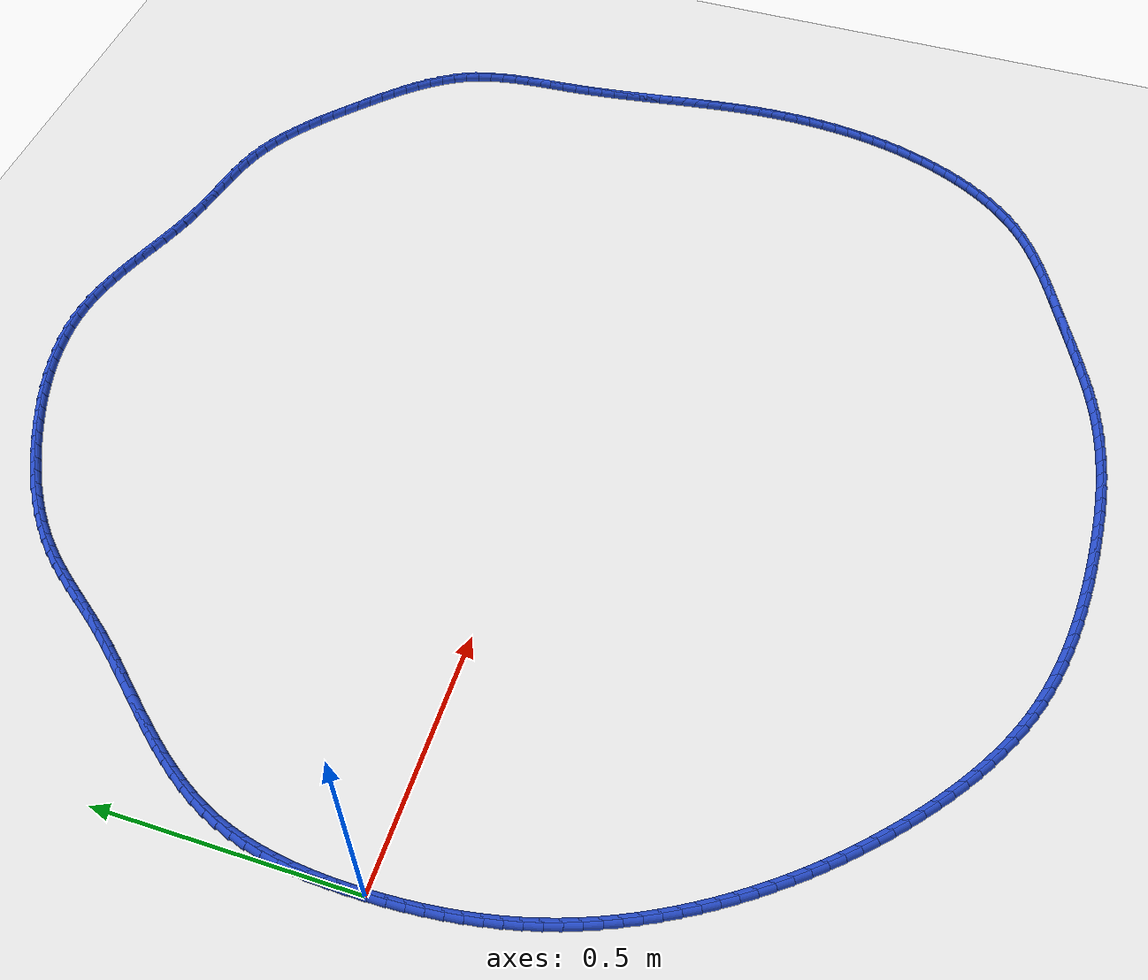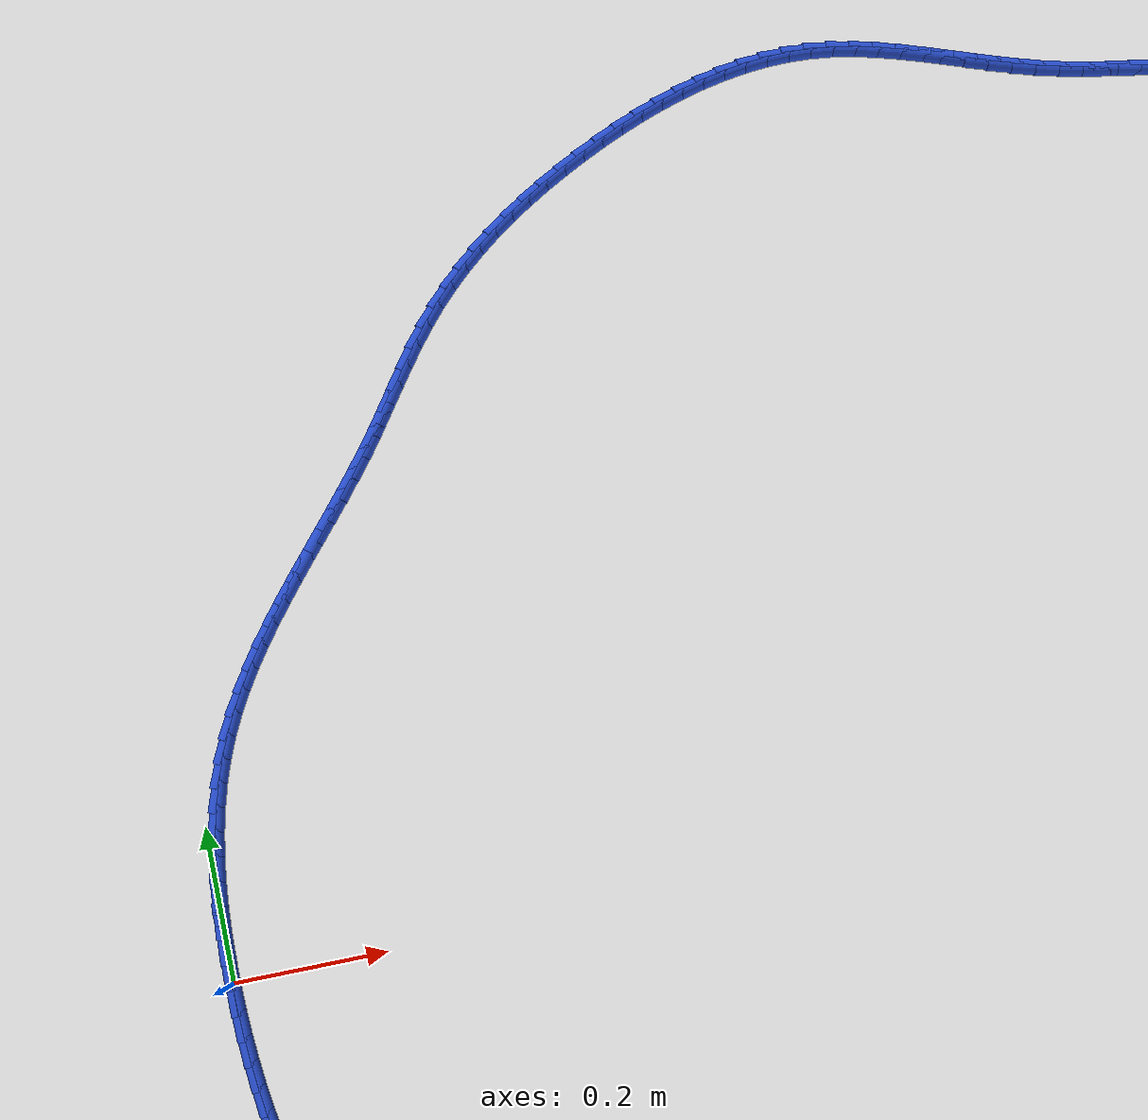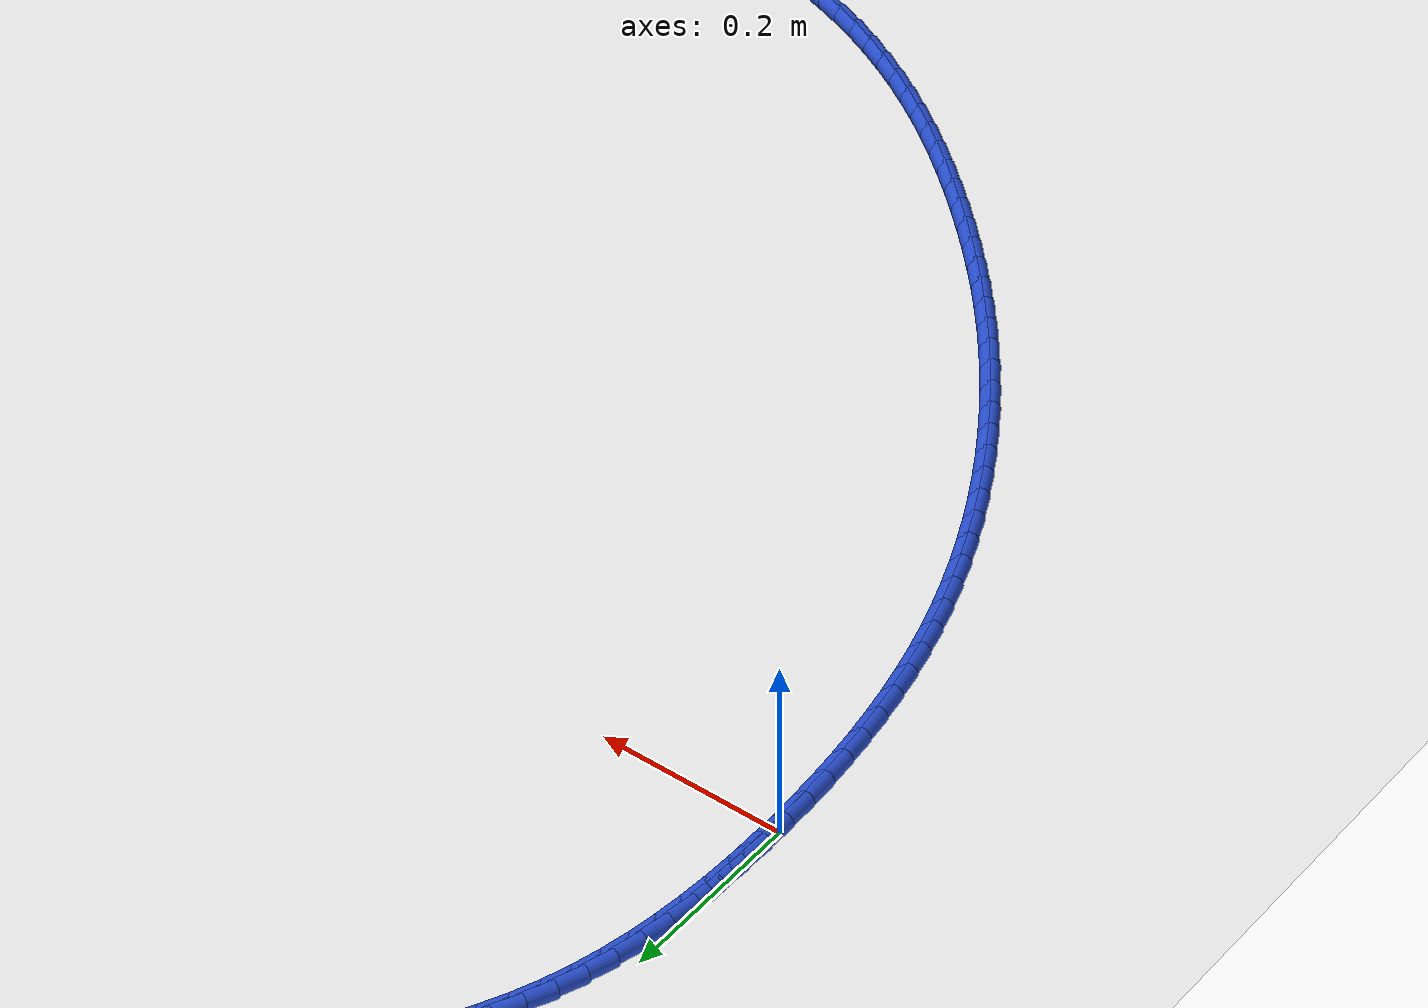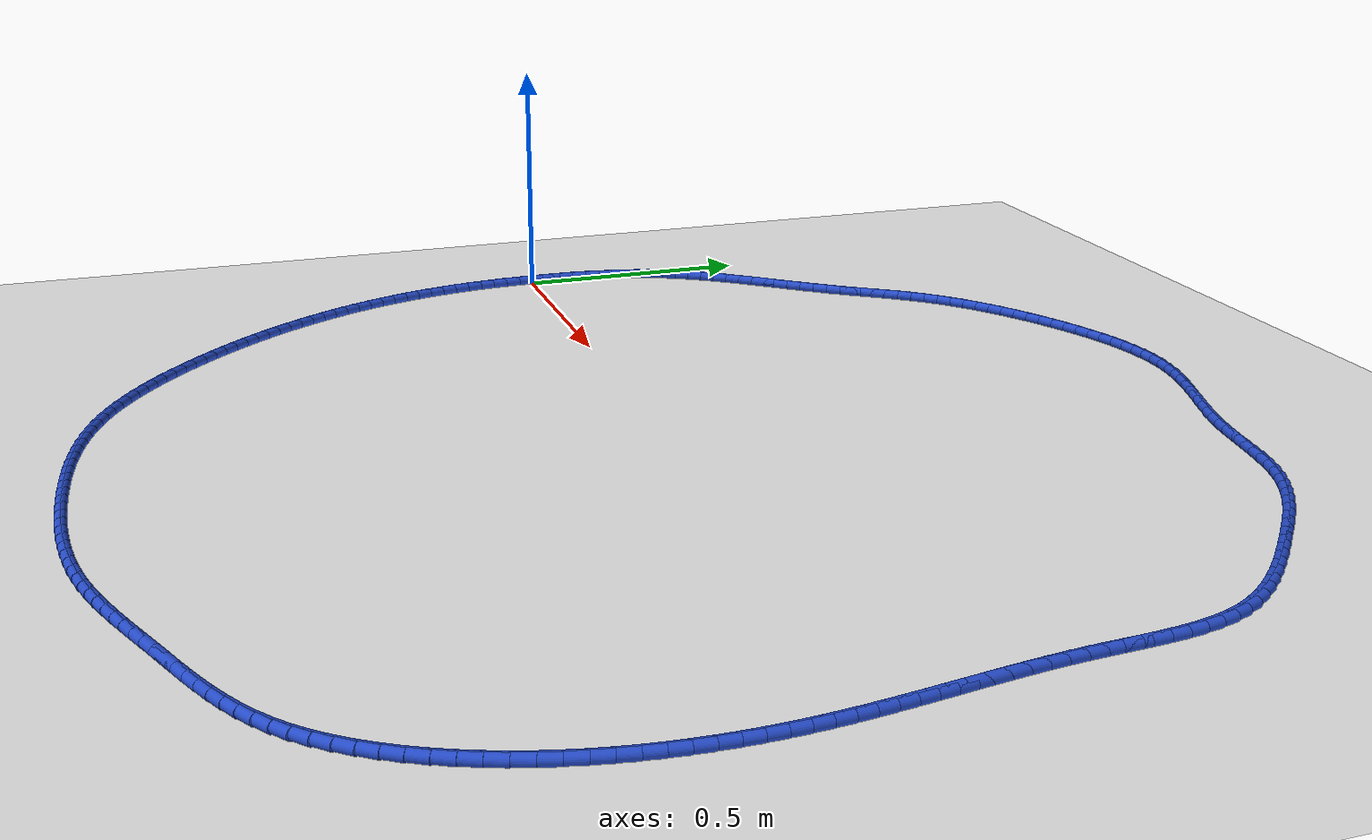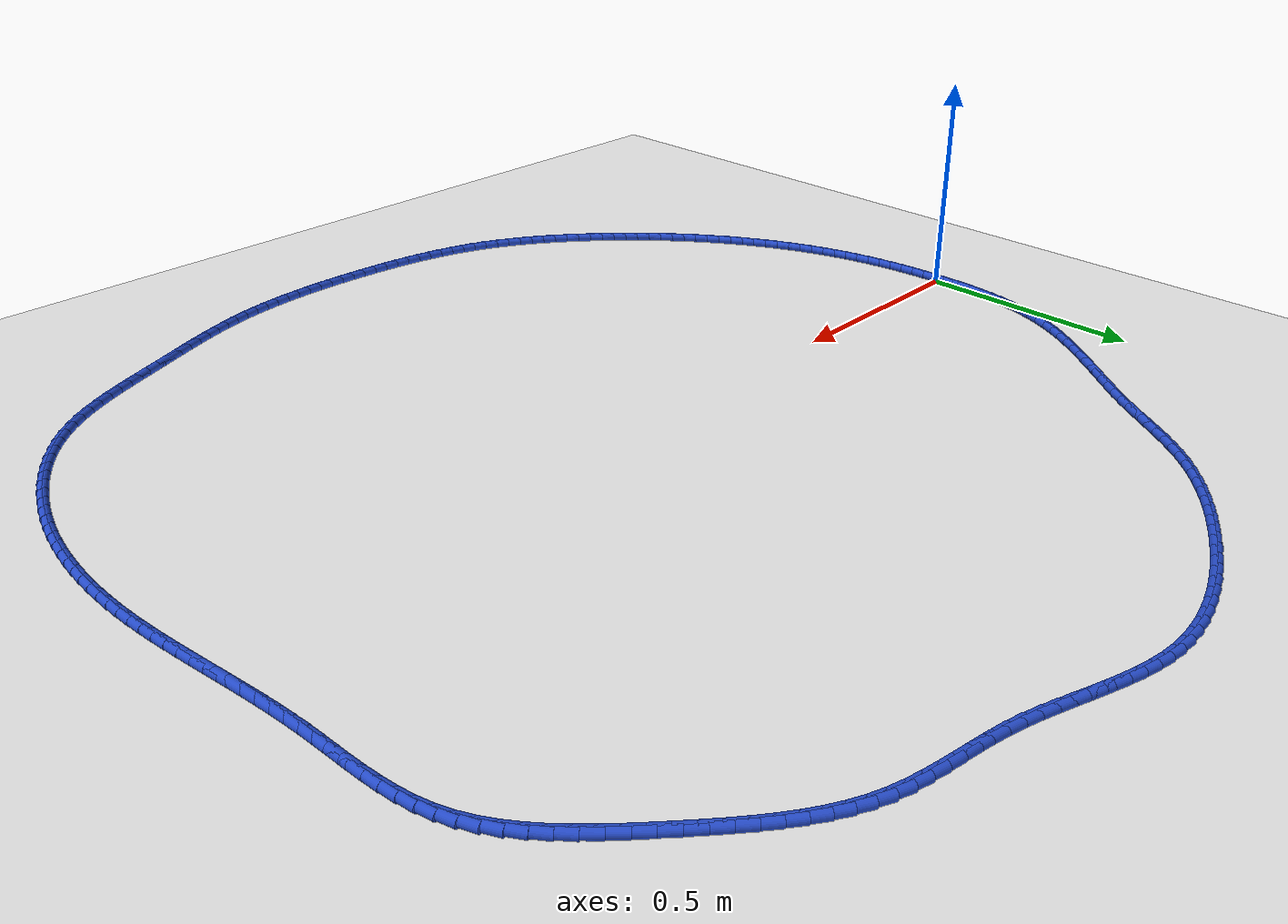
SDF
<sdf version="1.6">
 <world name="default">
  <light name="sun" type="directional">
   <pose>0 0 10 0 -0 0</pose>
   <diffuse>0.8 0.8 0.8 1</diffuse>
   <specular>0.2 0.2 0.2 1</specular>
   <attenuation>
    <range>1000</range>
    <constant>0.9</constant>
    <linear>0.01</linear>
    <quadratic>0.001</quadratic>
   </attenuation>
   <direction>-0.5 0.1 -0.9</direction>
  </light>
  <model name="ground_plane">
   <static>1</static>
   <link name="link">
    <collision name="collision">
     <geometry><plane><normal>0 0 1</normal><size>100 100</size></plane></geometry>
     <surface><friction><ode><mu>100</mu><mu2>50</mu2></ode></friction></surface>
    </collision>
    <visual name="visual">
     <cast_shadows>0</cast_shadows>
     <geometry><plane><normal>0 0 1</normal><size>100 100</size></plane></geometry>
     <material>
      <script><uri>file://media/materials/scripts/gazebo.material</uri><name>Gazebo/WhiteGlow</name></script>
     </material>
    </visual>
   </link>
  </model>
  <gravity>0 0 -9.8</gravity>
  <magnetic_field>6e-06 2.3e-05 -4.2e-05</magnetic_field>
  <atmosphere type="adiabatic"/>
  <physics name="default_physics" default="0" type="ode">
   <max_step_size>0.001</max_step_size>
   <real_time_factor>1</real_time_factor>
   <real_time_update_rate>1000</real_time_update_rate>
  </physics>
  <scene><ambient>0.4 0.4 0.4 1</ambient><background>0.7 0.7 0.7 1</background><shadows>1</shadows></scene>
  <spherical_coordinates>
   <surface_model>EARTH_WGS84</surface_model>
   <latitude_deg>0</latitude_deg>
   <longitude_deg>0</longitude_deg>
   <elevation>0</elevation>
   <heading_deg>0</heading_deg>
  </spherical_coordinates>
  <model name="line">
   <link name="link_0">
    <pose>2.2551405187698492e-17 6.245004513516506e-17 0.01 0 1.57 -1.5640277802827918</pose>
    <collision name="collision">
     <geometry><cylinder><radius>0.01</radius><length>0.08</length></cylinder></geometry>
    </collision>
    <visual name="visual">
     <material>
      <script><name>Gazebo/Blue</name><uri>file://media/materials/scripts/gazebo.material</uri></script>
     </material>
     <geometry><cylinder><radius>0.01</radius><length>0.08</length></cylinder></geometry>
    </visual>
   </link>
   <link name="link_1">
    <pose>-0.00021804687882136633 0.03221423515539994 0.01 0 1.57 1.550294958255304</pose>
    <collision name="collision">
     <geometry><cylinder><radius>0.01</radius><length>0.08</length></cylinder></geometry>
    </collision>
    <visual name="visual">
     <material>
      <script><name>Gazebo/Blue</name><uri>file://media/materials/scripts/gazebo.material</uri></script>
     </material>
     <geometry><cylinder><radius>0.01</radius><length>0.08</length></cylinder></geometry>
    </visual>
   </link>
   <link name="link_2">
    <pose>0.00044337836184048755 0.06447220709343172 0.01 0 1.57 1.5193624895453874</pose>
    <collision name="collision">
     <geometry><cylinder><radius>0.01</radius><length>0.08</length></cylinder></geometry>
    </collision>
    <visual name="visual">
     <material>
      <script><name>Gazebo/Blue</name><uri>file://media/materials/scripts/gazebo.material</uri></script>
     </material>
     <geometry><cylinder><radius>0.01</radius><length>0.08</length></cylinder></geometry>
    </visual>
   </link>
   <link name="link_3">
    <pose>0.002100509430965067 0.09666248531929927 0.01 0 1.57 1.4845078215723275</pose>
    <collision name="collision">
     <geometry><cylinder><radius>0.01</radius><length>0.08</length></cylinder></geometry>
    </collision>
    <visual name="visual">
     <material>
      <script><name>Gazebo/Blue</name><uri>file://media/materials/scripts/gazebo.material</uri></script>
     </material>
     <geometry><cylinder><radius>0.01</radius><length>0.08</length></cylinder></geometry>
    </visual>
   </link>
   <link name="link_4">
    <pose>0.004869580037531858 0.12867363933820639 0.01 0 1.57 1.4454429252567342</pose>
    <collision name="collision">
     <geometry><cylinder><radius>0.01</radius><length>0.08</length></cylinder></geometry>
    </collision>
    <visual name="visual">
     <material>
      <script><name>Gazebo/Blue</name><uri>file://media/materials/scripts/gazebo.material</uri></script>
     </material>
     <geometry><cylinder><radius>0.01</radius><length>0.08</length></cylinder></geometry>
    </visual>
   </link>
   <link name="link_5">
    <pose>0.008866823890520344 0.16039423865535699 0.01 0 1.57 1.401863563391801</pose>
    <collision name="collision">
     <geometry><cylinder><radius>0.01</radius><length>0.08</length></cylinder></geometry>
    </collision>
    <visual name="visual">
     <material>
      <script><name>Gazebo/Blue</name><uri>file://media/materials/scripts/gazebo.material</uri></script>
     </material>
     <geometry><cylinder><radius>0.01</radius><length>0.08</length></cylinder></geometry>
    </visual>
   </link>
   <link name="link_6">
    <pose>0.014208474698910012 0.19171285277595485 0.01 0 1.57 1.3534674927857533</pose>
    <collision name="collision">
     <geometry><cylinder><radius>0.01</radius><length>0.08</length></cylinder></geometry>
    </collision>
    <visual name="visual">
     <material>
      <script><name>Gazebo/Blue</name><uri>file://media/materials/scripts/gazebo.material</uri></script>
     </material>
     <geometry><cylinder><radius>0.01</radius><length>0.08</length></cylinder></geometry>
    </visual>
   </link>
   <link name="link_7">
    <pose>0.02101076617168035 0.22251805120520388 0.01 0 1.57 1.2999806855689242</pose>
    <collision name="collision">
     <geometry><cylinder><radius>0.01</radius><length>0.08</length></cylinder></geometry>
    </collision>
    <visual name="visual">
     <material>
      <script><name>Gazebo/Blue</name><uri>file://media/materials/scripts/gazebo.material</uri></script>
     </material>
     <geometry><cylinder><radius>0.01</radius><length>0.08</length></cylinder></geometry>
    </visual>
   </link>
   <link name="link_8">
    <pose>0.02938993201781083 0.25269840344830774 0.01 0 1.57 1.2411931809515189</pose>
    <collision name="collision">
     <geometry><cylinder><radius>0.01</radius><length>0.08</length></cylinder></geometry>
    </collision>
    <visual name="visual">
     <material>
      <script><name>Gazebo/Blue</name><uri>file://media/materials/scripts/gazebo.material</uri></script>
     </material>
     <geometry><cylinder><radius>0.01</radius><length>0.08</length></cylinder></geometry>
    </visual>
   </link>
   <link name="link_9">
    <pose>0.03946220594628094 0.28214247901047046 0.01 0 1.57 1.1773535749368804</pose>
    <collision name="collision">
     <geometry><cylinder><radius>0.01</radius><length>0.08</length></cylinder></geometry>
    </collision>
    <visual name="visual">
     <material>
      <script><name>Gazebo/Blue</name><uri>file://media/materials/scripts/gazebo.material</uri></script>
     </material>
     <geometry><cylinder><radius>0.01</radius><length>0.08</length></cylinder></geometry>
    </visual>
   </link>
   <link name="link_10">
    <pose>0.051334707038882654 0.3107450504873547 0.01 0 1.57 1.114690556031248</pose>
    <collision name="collision">
     <geometry><cylinder><radius>0.01</radius><length>0.08</length></cylinder></geometry>
    </collision>
    <visual name="visual">
     <material>
      <script><name>Gazebo/Blue</name><uri>file://media/materials/scripts/gazebo.material</uri></script>
     </material>
     <geometry><cylinder><radius>0.01</radius><length>0.08</length></cylinder></geometry>
    </visual>
   </link>
   <link name="link_11">
    <pose>0.06495586619032379 0.33850888799980716 0.01 0 1.57 1.0588263026917826</pose>
    <collision name="collision">
     <geometry><cylinder><radius>0.01</radius><length>0.08</length></cylinder></geometry>
    </collision>
    <visual name="visual">
     <material>
      <script><name>Gazebo/Blue</name><uri>file://media/materials/scripts/gazebo.material</uri></script>
     </material>
     <geometry><cylinder><radius>0.01</radius><length>0.08</length></cylinder></geometry>
    </visual>
   </link>
   <link name="link_12">
    <pose>0.08013943676492061 0.3655284183965478 0.01 0 1.57 1.0102194662250645</pose>
    <collision name="collision">
     <geometry><cylinder><radius>0.01</radius><length>0.08</length></cylinder></geometry>
    </collision>
    <visual name="visual">
     <material>
      <script><name>Gazebo/Blue</name><uri>file://media/materials/scripts/gazebo.material</uri></script>
     </material>
     <geometry><cylinder><radius>0.01</radius><length>0.08</length></cylinder></geometry>
    </visual>
   </link>
   <link name="link_13">
    <pose>0.09669490018429547 0.39190097585826017 0.01 0 1.57 0.9689408644709877</pose>
    <collision name="collision">
     <geometry><cylinder><radius>0.01</radius><length>0.08</length></cylinder></geometry>
    </collision>
    <visual name="visual">
     <material>
      <script><name>Gazebo/Blue</name><uri>file://media/materials/scripts/gazebo.material</uri></script>
     </material>
     <geometry><cylinder><radius>0.01</radius><length>0.08</length></cylinder></geometry>
    </visual>
   </link>
   <link name="link_14">
    <pose>0.11443173787007076 0.41772389456562875 0.01 0 1.57 0.9349128984346179</pose>
    <collision name="collision">
     <geometry><cylinder><radius>0.01</radius><length>0.08</length></cylinder></geometry>
    </collision>
    <visual name="visual">
     <material>
      <script><name>Gazebo/Blue</name><uri>file://media/materials/scripts/gazebo.material</uri></script>
     </material>
     <geometry><cylinder><radius>0.01</radius><length>0.08</length></cylinder></geometry>
    </visual>
   </link>
   <link name="link_15">
    <pose>0.13315943124386873 0.44309450869933714 0.01 0 1.57 0.9079767573073776</pose>
    <collision name="collision">
     <geometry><cylinder><radius>0.01</radius><length>0.08</length></cylinder></geometry>
    </collision>
    <visual name="visual">
     <material>
      <script><name>Gazebo/Blue</name><uri>file://media/materials/scripts/gazebo.material</uri></script>
     </material>
     <geometry><cylinder><radius>0.01</radius><length>0.08</length></cylinder></geometry>
    </visual>
   </link>
   <link name="link_16">
    <pose>0.15268746172731182 0.4681101524400696 0.01 0 1.57 0.8879455333379783</pose>
    <collision name="collision">
     <geometry><cylinder><radius>0.01</radius><length>0.08</length></cylinder></geometry>
    </collision>
    <visual name="visual">
     <material>
      <script><name>Gazebo/Blue</name><uri>file://media/materials/scripts/gazebo.material</uri></script>
     </material>
     <geometry><cylinder><radius>0.01</radius><length>0.08</length></cylinder></geometry>
    </visual>
   </link>
   <link name="link_17">
    <pose>0.17282531074202226 0.49286815996851 0.01 0 1.57 0.874642692186686</pose>
    <collision name="collision">
     <geometry><cylinder><radius>0.01</radius><length>0.08</length></cylinder></geometry>
    </collision>
    <visual name="visual">
     <material>
      <script><name>Gazebo/Blue</name><uri>file://media/materials/scripts/gazebo.material</uri></script>
     </material>
     <geometry><cylinder><radius>0.01</radius><length>0.08</length></cylinder></geometry>
    </visual>
   </link>
   <link name="link_18">
    <pose>0.1933824597096225 0.5174658654653426 0.01 0 1.57 0.8679276673018819</pose>
    <collision name="collision">
     <geometry><cylinder><radius>0.01</radius><length>0.08</length></cylinder></geometry>
    </collision>
    <visual name="visual">
     <material>
      <script><name>Gazebo/Blue</name><uri>file://media/materials/scripts/gazebo.material</uri></script>
     </material>
     <geometry><cylinder><radius>0.01</radius><length>0.08</length></cylinder></geometry>
    </visual>
   </link>
   <link name="link_19">
    <pose>0.21416839005173482 0.5420006031112512 0.01 0 1.57 0.8677109606641003</pose>
    <collision name="collision">
     <geometry><cylinder><radius>0.01</radius><length>0.08</length></cylinder></geometry>
    </collision>
    <visual name="visual">
     <material>
      <script><name>Gazebo/Blue</name><uri>file://media/materials/scripts/gazebo.material</uri></script>
     </material>
     <geometry><cylinder><radius>0.01</radius><length>0.08</length></cylinder></geometry>
    </visual>
   </link>
   <link name="link_20">
    <pose>0.23499258318998162 0.5665697070869198 0.01 0 1.57 0.8739607717565215</pose>
    <collision name="collision">
     <geometry><cylinder><radius>0.01</radius><length>0.08</length></cylinder></geometry>
    </collision>
    <visual name="visual">
     <material>
      <script><name>Gazebo/Blue</name><uri>file://media/materials/scripts/gazebo.material</uri></script>
     </material>
     <geometry><cylinder><radius>0.01</radius><length>0.08</length></cylinder></geometry>
    </visual>
   </link>
   <link name="link_21">
    <pose>0.2556645205459852 0.5912705115730326 0.01 0 1.57 0.886702367492394</pose>
    <collision name="collision">
     <geometry><cylinder><radius>0.01</radius><length>0.08</length></cylinder></geometry>
    </collision>
    <visual name="visual">
     <material>
      <script><name>Gazebo/Blue</name><uri>file://media/materials/scripts/gazebo.material</uri></script>
     </material>
     <geometry><cylinder><radius>0.01</radius><length>0.08</length></cylinder></geometry>
    </visual>
   </link>
   <link name="link_22">
    <pose>0.27599368354136783 0.6162003507502734 0.01 0 1.57 0.9060104577766708</pose>
    <collision name="collision">
     <geometry><cylinder><radius>0.01</radius><length>0.08</length></cylinder></geometry>
    </collision>
    <visual name="visual">
     <material>
      <script><name>Gazebo/Blue</name><uri>file://media/materials/scripts/gazebo.material</uri></script>
     </material>
     <geometry><cylinder><radius>0.01</radius><length>0.08</length></cylinder></geometry>
    </visual>
   </link>
   <link name="link_23">
    <pose>0.29578955359775205 0.6414565587993264 0.01 0 1.57 0.9312137643740723</pose>
    <collision name="collision">
     <geometry><cylinder><radius>0.01</radius><length>0.08</length></cylinder></geometry>
    </collision>
    <visual name="visual">
     <material>
      <script><name>Gazebo/Blue</name><uri>file://media/materials/scripts/gazebo.material</uri></script>
     </material>
     <geometry><cylinder><radius>0.01</radius><length>0.08</length></cylinder></geometry>
    </visual>
   </link>
   <link name="link_24">
    <pose>0.3148822085674277 0.6671223453819348 0.01 0 1.57 0.9516073168095652</pose>
    <collision name="collision">
     <geometry><cylinder><radius>0.01</radius><length>0.08</length></cylinder></geometry>
    </collision>
    <visual name="visual">
     <material>
      <script><name>Gazebo/Blue</name><uri>file://media/materials/scripts/gazebo.material</uri></script>
     </material>
     <geometry><cylinder><radius>0.01</radius><length>0.08</length></cylinder></geometry>
    </visual>
   </link>
   <link name="link_25">
    <pose>0.3333860713298848 0.693085923425355 0.01 0 1.57 0.9592552546301093</pose>
    <collision name="collision">
     <geometry><cylinder><radius>0.01</radius><length>0.08</length></cylinder></geometry>
    </collision>
    <visual name="visual">
     <material>
      <script><name>Gazebo/Blue</name><uri>file://media/materials/scripts/gazebo.material</uri></script>
     </material>
     <geometry><cylinder><radius>0.01</radius><length>0.08</length></cylinder></geometry>
    </visual>
   </link>
   <link name="link_26">
    <pose>0.3516228686630927 0.7190933420087593 0.01 0 1.57 0.9538451383325849</pose>
    <collision name="collision">
     <geometry><cylinder><radius>0.01</radius><length>0.08</length></cylinder></geometry>
    </collision>
    <visual name="visual">
     <material>
      <script><name>Gazebo/Blue</name><uri>file://media/materials/scripts/gazebo.material</uri></script>
     </material>
     <geometry><cylinder><radius>0.01</radius><length>0.08</length></cylinder></geometry>
    </visual>
   </link>
   <link name="link_27">
    <pose>0.3699190316049898 0.7448874241470527 0.01 0 1.57 0.9351942945684564</pose>
    <collision name="collision">
     <geometry><cylinder><radius>0.01</radius><length>0.08</length></cylinder></geometry>
    </collision>
    <visual name="visual">
     <material>
      <script><name>Gazebo/Blue</name><uri>file://media/materials/scripts/gazebo.material</uri></script>
     </material>
     <geometry><cylinder><radius>0.01</radius><length>0.08</length></cylinder></geometry>
    </visual>
   </link>
   <link name="link_28">
    <pose>0.3886009911935139 0.7702109928551397 0.01 0 1.57 0.90309856681486</pose>
    <collision name="collision">
     <geometry><cylinder><radius>0.01</radius><length>0.08</length></cylinder></geometry>
    </collision>
    <visual name="visual">
     <material>
      <script><name>Gazebo/Blue</name><uri>file://media/materials/scripts/gazebo.material</uri></script>
     </material>
     <geometry><cylinder><radius>0.01</radius><length>0.08</length></cylinder></geometry>
    </visual>
   </link>
   <link name="link_29">
    <pose>0.4079951784666028 0.7948068711479248 0.01 0 1.57 0.8574647933892661</pose>
    <collision name="collision">
     <geometry><cylinder><radius>0.01</radius><length>0.08</length></cylinder></geometry>
    </collision>
    <visual name="visual">
     <material>
      <script><name>Gazebo/Blue</name><uri>file://media/materials/scripts/gazebo.material</uri></script>
     </material>
     <geometry><cylinder><radius>0.01</radius><length>0.08</length></cylinder></geometry>
    </visual>
   </link>
   <link name="link_30">
    <pose>0.42842721465625355 0.8184184916501661 0.01 0 1.57 0.8033062774453298</pose>
    <collision name="collision">
     <geometry><cylinder><radius>0.01</radius><length>0.08</length></cylinder></geometry>
    </collision>
    <visual name="visual">
     <material>
      <script><name>Gazebo/Blue</name><uri>file://media/materials/scripts/gazebo.material</uri></script>
     </material>
     <geometry><cylinder><radius>0.01</radius><length>0.08</length></cylinder></geometry>
    </visual>
   </link>
   <link name="link_31">
    <pose>0.4500999522898263 0.8408817054392804 0.01 0 1.57 0.7509801072675774</pose>
    <collision name="collision">
     <geometry><cylinder><radius>0.01</radius><length>0.08</length></cylinder></geometry>
    </collision>
    <visual name="visual">
     <material>
      <script><name>Gazebo/Blue</name><uri>file://media/materials/scripts/gazebo.material</uri></script>
     </material>
     <geometry><cylinder><radius>0.01</radius><length>0.08</length></cylinder></geometry>
    </visual>
   </link>
   <link name="link_32">
    <pose>0.47296315898855296 0.8622228821412431 0.01 0 1.57 0.7018883308049515</pose>
    <collision name="collision">
     <geometry><cylinder><radius>0.01</radius><length>0.08</length></cylinder></geometry>
    </collision>
    <visual name="visual">
     <material>
      <script><name>Gazebo/Blue</name><uri>file://media/materials/scripts/gazebo.material</uri></script>
     </material>
     <geometry><cylinder><radius>0.01</radius><length>0.08</length></cylinder></geometry>
    </visual>
   </link>
   <link name="link_33">
    <pose>0.49693536993535103 0.8824919026964977 0.01 0 1.57 0.6561018103679742</pose>
    <collision name="collision">
     <geometry><cylinder><radius>0.01</radius><length>0.08</length></cylinder></geometry>
    </collision>
    <visual name="visual">
     <material>
      <script><name>Gazebo/Blue</name><uri>file://media/materials/scripts/gazebo.material</uri></script>
     </material>
     <geometry><cylinder><radius>0.01</radius><length>0.08</length></cylinder></geometry>
    </visual>
   </link>
   <link name="link_34">
    <pose>0.5219351203131383 0.9017386480454888 0.01 0 1.57 0.6136242464177583</pose>
    <collision name="collision">
     <geometry><cylinder><radius>0.01</radius><length>0.08</length></cylinder></geometry>
    </collision>
    <visual name="visual">
     <material>
      <script><name>Gazebo/Blue</name><uri>file://media/materials/scripts/gazebo.material</uri></script>
     </material>
     <geometry><cylinder><radius>0.01</radius><length>0.08</length></cylinder></geometry>
    </visual>
   </link>
   <link name="link_35">
    <pose>0.5478809453048326 0.9200129991286612 0.01 0 1.57 0.5744076051759945</pose>
    <collision name="collision">
     <geometry><cylinder><radius>0.01</radius><length>0.08</length></cylinder></geometry>
    </collision>
    <visual name="visual">
     <material>
      <script><name>Gazebo/Blue</name><uri>file://media/materials/scripts/gazebo.material</uri></script>
     </material>
     <geometry><cylinder><radius>0.01</radius><length>0.08</length></cylinder></geometry>
    </visual>
   </link>
   <link name="link_36">
    <pose>0.5746913800933513 0.9373648368864588 0.01 0 1.57 0.5383666690072105</pose>
    <collision name="collision">
     <geometry><cylinder><radius>0.01</radius><length>0.08</length></cylinder></geometry>
    </collision>
    <visual name="visual">
     <material>
      <script><name>Gazebo/Blue</name><uri>file://media/materials/scripts/gazebo.material</uri></script>
     </material>
     <geometry><cylinder><radius>0.01</radius><length>0.08</length></cylinder></geometry>
    </visual>
   </link>
   <link name="link_37">
    <pose>0.6022849598616123 0.9538440422593262 0.01 0 1.57 0.5053918472926673</pose>
    <collision name="collision">
     <geometry><cylinder><radius>0.01</radius><length>0.08</length></cylinder></geometry>
    </collision>
    <visual name="visual">
     <material>
      <script><name>Gazebo/Blue</name><uri>file://media/materials/scripts/gazebo.material</uri></script>
     </material>
     <geometry><cylinder><radius>0.01</radius><length>0.08</length></cylinder></geometry>
    </visual>
   </link>
   <link name="link_38">
    <pose>0.6305802197925333 0.9695004961877077 0.01 0 1.57 0.4753598841261037</pose>
    <collision name="collision">
     <geometry><cylinder><radius>0.01</radius><length>0.08</length></cylinder></geometry>
    </collision>
    <visual name="visual">
     <material>
      <script><name>Gazebo/Blue</name><uri>file://media/materials/scripts/gazebo.material</uri></script>
     </material>
     <geometry><cylinder><radius>0.01</radius><length>0.08</length></cylinder></geometry>
    </visual>
   </link>
   <link name="link_39">
    <pose>0.659495695069032 0.984384079612048 0.01 0 1.57 0.44732672768013937</pose>
    <collision name="collision">
     <geometry><cylinder><radius>0.01</radius><length>0.08</length></cylinder></geometry>
    </collision>
    <visual name="visual">
     <material>
      <script><name>Gazebo/Blue</name><uri>file://media/materials/scripts/gazebo.material</uri></script>
     </material>
     <geometry><cylinder><radius>0.01</radius><length>0.08</length></cylinder></geometry>
    </visual>
   </link>
   <link name="link_40">
    <pose>0.6889512959813663 0.9985157649912986 0.01 0 1.57 0.417384771851742</pose>
    <collision name="collision">
     <geometry><cylinder><radius>0.01</radius><length>0.08</length></cylinder></geometry>
    </collision>
    <visual name="visual">
     <material>
      <script><name>Gazebo/Blue</name><uri>file://media/materials/scripts/gazebo.material</uri></script>
     </material>
     <geometry><cylinder><radius>0.01</radius><length>0.08</length></cylinder></geometry>
    </visual>
   </link>
   <link name="link_41">
    <pose>0.7188732211885388 1.0117843262380575 0.01 0 1.57 0.38419602977444756</pose>
    <collision name="collision">
     <geometry><cylinder><radius>0.01</radius><length>0.08</length></cylinder></geometry>
    </collision>
    <visual name="visual">
     <material>
      <script><name>Gazebo/Blue</name><uri>file://media/materials/scripts/gazebo.material</uri></script>
     </material>
     <geometry><cylinder><radius>0.01</radius><length>0.08</length></cylinder></geometry>
    </visual>
   </link>
   <link name="link_42">
    <pose>0.7491894658521274 1.0240407699140095 0.01 0 1.57 0.3474453531147877</pose>
    <collision name="collision">
     <geometry><cylinder><radius>0.01</radius><length>0.08</length></cylinder></geometry>
    </collision>
    <visual name="visual">
     <material>
      <script><name>Gazebo/Blue</name><uri>file://media/materials/scripts/gazebo.material</uri></script>
     </material>
     <geometry><cylinder><radius>0.01</radius><length>0.08</length></cylinder></geometry>
    </visual>
   </link>
   <link name="link_43">
    <pose>0.7798280252733434 1.035136099645379 0.01 0 1.57 0.3067864797603333</pose>
    <collision name="collision">
     <geometry><cylinder><radius>0.01</radius><length>0.08</length></cylinder></geometry>
    </collision>
    <visual name="visual">
     <material>
      <script><name>Gazebo/Blue</name><uri>file://media/materials/scripts/gazebo.material</uri></script>
     </material>
     <geometry><cylinder><radius>0.01</radius><length>0.08</length></cylinder></geometry>
    </visual>
   </link>
   <link name="link_44">
    <pose>0.8107168947533977 1.0449213190583901 0.01 0 1.57 0.26185009065658865</pose>
    <collision name="collision">
     <geometry><cylinder><radius>0.01</radius><length>0.08</length></cylinder></geometry>
    </collision>
    <visual name="visual">
     <material>
      <script><name>Gazebo/Blue</name><uri>file://media/materials/scripts/gazebo.material</uri></script>
     </material>
     <geometry><cylinder><radius>0.01</radius><length>0.08</length></cylinder></geometry>
    </visual>
   </link>
   <link name="link_45">
    <pose>0.8417840695935013 1.0532474317792673 0.01 0 1.57 0.21225787239913654</pose>
    <collision name="collision">
     <geometry><cylinder><radius>0.01</radius><length>0.08</length></cylinder></geometry>
    </collision>
    <visual name="visual">
     <material>
      <script><name>Gazebo/Blue</name><uri>file://media/materials/scripts/gazebo.material</uri></script>
     </material>
     <geometry><cylinder><radius>0.01</radius><length>0.08</length></cylinder></geometry>
    </visual>
   </link>
   <link name="link_46">
    <pose>0.8729575450948656 1.0599654414342345 0.01 0 1.57 0.15764489733930329</pose>
    <collision name="collision">
     <geometry><cylinder><radius>0.01</radius><length>0.08</length></cylinder></geometry>
    </collision>
    <visual name="visual">
     <material>
      <script><name>Gazebo/Blue</name><uri>file://media/materials/scripts/gazebo.material</uri></script>
     </material>
     <geometry><cylinder><radius>0.01</radius><length>0.08</length></cylinder></geometry>
    </visual>
   </link>
   <link name="link_47">
    <pose>0.904165316558701 1.064926351649516 0.01 0 1.57 0.09769277592915032</pose>
    <collision name="collision">
     <geometry><cylinder><radius>0.01</radius><length>0.08</length></cylinder></geometry>
    </collision>
    <visual name="visual">
     <material>
      <script><name>Gazebo/Blue</name><uri>file://media/materials/scripts/gazebo.material</uri></script>
     </material>
     <geometry><cylinder><radius>0.01</radius><length>0.08</length></cylinder></geometry>
    </visual>
   </link>
   <link name="link_48">
    <pose>0.9353353792862192 1.067981166051336 0.01 0 1.57 0.032175336893997</pose>
    <collision name="collision">
     <geometry><cylinder><radius>0.01</radius><length>0.08</length></cylinder></geometry>
    </collision>
    <visual name="visual">
     <material>
      <script><name>Gazebo/Blue</name><uri>file://media/materials/scripts/gazebo.material</uri></script>
     </material>
     <geometry><cylinder><radius>0.01</radius><length>0.08</length></cylinder></geometry>
    </visual>
   </link>
   <link name="link_49">
    <pose>0.9663957285786312 1.068980888265919 0.01 0 1.57 -0.038983469901849005</pose>
    <collision name="collision">
     <geometry><cylinder><radius>0.01</radius><length>0.08</length></cylinder></geometry>
    </collision>
    <visual name="visual">
     <material>
      <script><name>Gazebo/Blue</name><uri>file://media/materials/scripts/gazebo.material</uri></script>
     </material>
     <geometry><cylinder><radius>0.01</radius><length>0.08</length></cylinder></geometry>
    </visual>
   </link>
   <link name="link_50">
    <pose>0.9972743597371475 1.0677765219194888 0.01 0 1.57 -0.11418028895818372</pose>
    <collision name="collision">
     <geometry><cylinder><radius>0.01</radius><length>0.08</length></cylinder></geometry>
    </collision>
    <visual name="visual">
     <material>
      <script><name>Gazebo/Blue</name><uri>file://media/materials/scripts/gazebo.material</uri></script>
     </material>
     <geometry><cylinder><radius>0.01</radius><length>0.08</length></cylinder></geometry>
    </visual>
   </link>
   <link name="link_51">
    <pose>1.0279104734216 1.0642632004338397 0.01 0 1.57 -0.18216826430119734</pose>
    <collision name="collision">
     <geometry><cylinder><radius>0.01</radius><length>0.08</length></cylinder></geometry>
    </collision>
    <visual name="visual">
     <material>
      <script><name>Gazebo/Blue</name><uri>file://media/materials/scripts/gazebo.material</uri></script>
     </material>
     <geometry><cylinder><radius>0.01</radius><length>0.08</length></cylinder></geometry>
    </visual>
   </link>
   <link name="link_52">
    <pose>1.058325629366141 1.0586604100012877 0.01 0 1.57 -0.23765354318313558</pose>
    <collision name="collision">
     <geometry><cylinder><radius>0.01</radius><length>0.08</length></cylinder></geometry>
    </collision>
    <visual name="visual">
     <material>
      <script><name>Gazebo/Blue</name><uri>file://media/materials/scripts/gazebo.material</uri></script>
     </material>
     <geometry><cylinder><radius>0.01</radius><length>0.08</length></cylinder></geometry>
    </visual>
   </link>
   <link name="link_53">
    <pose>1.088578123386184 1.051332313643428 0.01 0 1.57 -0.2805911259292073</pose>
    <collision name="collision">
     <geometry><cylinder><radius>0.01</radius><length>0.08</length></cylinder></geometry>
    </collision>
    <visual name="visual">
     <material>
      <script><name>Gazebo/Blue</name><uri>file://media/materials/scripts/gazebo.material</uri></script>
     </material>
     <geometry><cylinder><radius>0.01</radius><length>0.08</length></cylinder></geometry>
    </visual>
   </link>
   <link name="link_54">
    <pose>1.1187264208104912 1.042643741972216 0.01 0 1.57 -0.31125092091023554</pose>
    <collision name="collision">
     <geometry><cylinder><radius>0.01</radius><length>0.08</length></cylinder></geometry>
    </collision>
    <visual name="visual">
     <material>
      <script><name>Gazebo/Blue</name><uri>file://media/materials/scripts/gazebo.material</uri></script>
     </material>
     <geometry><cylinder><radius>0.01</radius><length>0.08</length></cylinder></geometry>
    </visual>
   </link>
   <link name="link_55">
    <pose>1.148828986967825 1.0329595255996094 0.01 0 1.57 -0.3299937959665748</pose>
    <collision name="collision">
     <geometry><cylinder><radius>0.01</radius><length>0.08</length></cylinder></geometry>
    </collision>
    <visual name="visual">
     <material>
      <script><name>Gazebo/Blue</name><uri>file://media/materials/scripts/gazebo.material</uri></script>
     </material>
     <geometry><cylinder><radius>0.01</radius><length>0.08</length></cylinder></geometry>
    </visual>
   </link>
   <link name="link_56">
    <pose>1.1789442871869484 1.0226444951375642 0.01 0 1.57 -0.3371392378755875</pose>
    <collision name="collision">
     <geometry><cylinder><radius>0.01</radius><length>0.08</length></cylinder></geometry>
    </collision>
    <visual name="visual">
     <material>
      <script><name>Gazebo/Blue</name><uri>file://media/materials/scripts/gazebo.material</uri></script>
     </material>
     <geometry><cylinder><radius>0.01</radius><length>0.08</length></cylinder></geometry>
    </visual>
   </link>
   <link name="link_57">
    <pose>1.2091307867966221 1.0120634811980376 0.01 0 1.57 -0.33289402226815085</pose>
    <collision name="collision">
     <geometry><cylinder><radius>0.01</radius><length>0.08</length></cylinder></geometry>
    </collision>
    <visual name="visual">
     <material>
      <script><name>Gazebo/Blue</name><uri>file://media/materials/scripts/gazebo.material</uri></script>
     </material>
     <geometry><cylinder><radius>0.01</radius><length>0.08</length></cylinder></geometry>
    </visual>
   </link>
   <link name="link_58">
    <pose>1.2394469511256094 1.0015813143929861 0.01 0 1.57 -0.31733000665880307</pose>
    <collision name="collision">
     <geometry><cylinder><radius>0.01</radius><length>0.08</length></cylinder></geometry>
    </collision>
    <visual name="visual">
     <material>
      <script><name>Gazebo/Blue</name><uri>file://media/materials/scripts/gazebo.material</uri></script>
     </material>
     <geometry><cylinder><radius>0.01</radius><length>0.08</length></cylinder></geometry>
    </visual>
   </link>
   <link name="link_59">
    <pose>1.2699512455026727 0.9915628253343665 0.01 0 1.57 -0.2904037225222117</pose>
    <collision name="collision">
     <geometry><cylinder><radius>0.01</radius><length>0.08</length></cylinder></geometry>
    </collision>
    <visual name="visual">
     <material>
      <script><name>Gazebo/Blue</name><uri>file://media/materials/scripts/gazebo.material</uri></script>
     </material>
     <geometry><cylinder><radius>0.01</radius><length>0.08</length></cylinder></geometry>
    </visual>
   </link>
   <link name="link_60">
    <pose>1.3007021352565744 0.9823728446341354 0.01 0 1.57 -0.25205179798326144</pose>
    <collision name="collision">
     <geometry><cylinder><radius>0.01</radius><length>0.08</length></cylinder></geometry>
    </collision>
    <visual name="visual">
     <material>
      <script><name>Gazebo/Blue</name><uri>file://media/materials/scripts/gazebo.material</uri></script>
     </material>
     <geometry><cylinder><radius>0.01</radius><length>0.08</length></cylinder></geometry>
    </visual>
   </link>
   <link name="link_61">
    <pose>1.3317577984635374 0.9743751217963575 0.01 0 1.57 -0.21007401955564767</pose>
    <collision name="collision">
     <geometry><cylinder><radius>0.01</radius><length>0.08</length></cylinder></geometry>
    </collision>
    <visual name="visual">
     <material>
      <script><name>Gazebo/Blue</name><uri>file://media/materials/scripts/gazebo.material</uri></script>
     </material>
     <geometry><cylinder><radius>0.01</radius><length>0.08</length></cylinder></geometry>
    </visual>
   </link>
   <link name="link_62">
    <pose>1.363111699380705 0.9676898484405105 0.01 0 1.57 -0.1821919166334967</pose>
    <collision name="collision">
     <geometry><cylinder><radius>0.01</radius><length>0.08</length></cylinder></geometry>
    </collision>
    <visual name="visual">
     <material>
      <script><name>Gazebo/Blue</name><uri>file://media/materials/scripts/gazebo.material</uri></script>
     </material>
     <geometry><cylinder><radius>0.01</radius><length>0.08</length></cylinder></geometry>
    </visual>
   </link>
   <link name="link_63">
    <pose>1.3946109964690374 0.9618865775322786 0.01 0 1.57 -0.17077191046090698</pose>
    <collision name="collision">
     <geometry><cylinder><radius>0.01</radius><length>0.08</length></cylinder></geometry>
    </collision>
    <visual name="visual">
     <material>
      <script><name>Gazebo/Blue</name><uri>file://media/materials/scripts/gazebo.material</uri></script>
     </material>
     <geometry><cylinder><radius>0.01</radius><length>0.08</length></cylinder></geometry>
    </visual>
   </link>
   <link name="link_64">
    <pose>1.4260827509179492 0.9564592236495564 0.01 0 1.57 -0.17588335814341197</pose>
    <collision name="collision">
     <geometry><cylinder><radius>0.01</radius><length>0.08</length></cylinder></geometry>
    </collision>
    <visual name="visual">
     <material>
      <script><name>Gazebo/Blue</name><uri>file://media/materials/scripts/gazebo.material</uri></script>
     </material>
     <geometry><cylinder><radius>0.01</radius><length>0.08</length></cylinder></geometry>
    </visual>
   </link>
   <link name="link_65">
    <pose>1.457354023916859 0.9509017013702384 0.01 0 1.57 -0.1978375962168804</pose>
    <collision name="collision">
     <geometry><cylinder><radius>0.01</radius><length>0.08</length></cylinder></geometry>
    </collision>
    <visual name="visual">
     <material>
      <script><name>Gazebo/Blue</name><uri>file://media/materials/scripts/gazebo.material</uri></script>
     </material>
     <geometry><cylinder><radius>0.01</radius><length>0.08</length></cylinder></geometry>
    </visual>
   </link>
   <link name="link_66">
    <pose>1.4882518766551822 0.9447079252722191 0.01 0 1.57 -0.23715673189919365</pose>
    <collision name="collision">
     <geometry><cylinder><radius>0.01</radius><length>0.08</length></cylinder></geometry>
    </collision>
    <visual name="visual">
     <material>
      <script><name>Gazebo/Blue</name><uri>file://media/materials/scripts/gazebo.material</uri></script>
     </material>
     <geometry><cylinder><radius>0.01</radius><length>0.08</length></cylinder></geometry>
    </visual>
   </link>
   <link name="link_67">
    <pose>1.5186033703223352 0.9373718099333933 0.01 0 1.57 -0.29439178246259684</pose>
    <collision name="collision">
     <geometry><cylinder><radius>0.01</radius><length>0.08</length></cylinder></geometry>
    </collision>
    <visual name="visual">
     <material>
      <script><name>Gazebo/Blue</name><uri>file://media/materials/scripts/gazebo.material</uri></script>
     </material>
     <geometry><cylinder><radius>0.01</radius><length>0.08</length></cylinder></geometry>
    </visual>
   </link>
   <link name="link_68">
    <pose>1.5482355661077347 0.9283872699316553 0.01 0 1.57 -0.36829055858154414</pose>
    <collision name="collision">
     <geometry><cylinder><radius>0.01</radius><length>0.08</length></cylinder></geometry>
    </collision>
    <visual name="visual">
     <material>
      <script><name>Gazebo/Blue</name><uri>file://media/materials/scripts/gazebo.material</uri></script>
     </material>
     <geometry><cylinder><radius>0.01</radius><length>0.08</length></cylinder></geometry>
    </visual>
   </link>
   <link name="link_69">
    <pose>1.5769912511873896 0.9172905126909958 0.01 0 1.57 -0.4431475086676228</pose>
    <collision name="collision">
     <geometry><cylinder><radius>0.01</radius><length>0.08</length></cylinder></geometry>
    </collision>
    <visual name="visual">
     <material>
      <script><name>Gazebo/Blue</name><uri>file://media/materials/scripts/gazebo.material</uri></script>
     </material>
     <geometry><cylinder><radius>0.01</radius><length>0.08</length></cylinder></geometry>
    </visual>
   </link>
   <link name="link_70">
    <pose>1.6048759991911818 0.9040555370833465 0.01 0 1.57 -0.509242013202018</pose>
    <collision name="collision">
     <geometry><cylinder><radius>0.01</radius><length>0.08</length></cylinder></geometry>
    </collision>
    <visual name="visual">
     <material>
      <script><name>Gazebo/Blue</name><uri>file://media/materials/scripts/gazebo.material</uri></script>
     </material>
     <geometry><cylinder><radius>0.01</radius><length>0.08</length></cylinder></geometry>
    </visual>
   </link>
   <link name="link_71">
    <pose>1.6319916184342993 0.8889151517354923 0.01 0 1.57 -0.5661393514712173</pose>
    <collision name="collision">
     <geometry><cylinder><radius>0.01</radius><length>0.08</length></cylinder></geometry>
    </collision>
    <visual name="visual">
     <material>
      <script><name>Gazebo/Blue</name><uri>file://media/materials/scripts/gazebo.material</uri></script>
     </material>
     <geometry><cylinder><radius>0.01</radius><length>0.08</length></cylinder></geometry>
    </visual>
   </link>
   <link name="link_72">
    <pose>1.6584411688008183 0.8721055311940688 0.01 0 1.57 -0.6138846072783865</pose>
    <collision name="collision">
     <geometry><cylinder><radius>0.01</radius><length>0.08</length></cylinder></geometry>
    </collision>
    <visual name="visual">
     <material>
      <script><name>Gazebo/Blue</name><uri>file://media/materials/scripts/gazebo.material</uri></script>
     </material>
     <geometry><cylinder><radius>0.01</radius><length>0.08</length></cylinder></geometry>
    </visual>
   </link>
   <link name="link_73">
    <pose>1.6843277101748158 0.8538628500057109 0.01 0 1.57 -0.6527399754456636</pose>
    <collision name="collision">
     <geometry><cylinder><radius>0.01</radius><length>0.08</length></cylinder></geometry>
    </collision>
    <visual name="visual">
     <material>
      <script><name>Gazebo/Blue</name><uri>file://media/materials/scripts/gazebo.material</uri></script>
     </material>
     <geometry><cylinder><radius>0.01</radius><length>0.08</length></cylinder></geometry>
    </visual>
   </link>
   <link name="link_74">
    <pose>1.7097543024403676 0.8344232827170543 0.01 0 1.57 -0.6830644278055301</pose>
    <collision name="collision">
     <geometry><cylinder><radius>0.01</radius><length>0.08</length></cylinder></geometry>
    </collision>
    <visual name="visual">
     <material>
      <script><name>Gazebo/Blue</name><uri>file://media/materials/scripts/gazebo.material</uri></script>
     </material>
     <geometry><cylinder><radius>0.01</radius><length>0.08</length></cylinder></geometry>
    </visual>
   </link>
   <link name="link_75">
    <pose>1.7348240054815502 0.8140230038747343 0.01 0 1.57 -0.7052263943187325</pose>
    <collision name="collision">
     <geometry><cylinder><radius>0.01</radius><length>0.08</length></cylinder></geometry>
    </collision>
    <visual name="visual">
     <material>
      <script><name>Gazebo/Blue</name><uri>file://media/materials/scripts/gazebo.material</uri></script>
     </material>
     <geometry><cylinder><radius>0.01</radius><length>0.08</length></cylinder></geometry>
    </visual>
   </link>
   <link name="link_76">
    <pose>1.7596398791824406 0.7928981880253855 0.01 0 1.57 -0.7195462570867244</pose>
    <collision name="collision">
     <geometry><cylinder><radius>0.01</radius><length>0.08</length></cylinder></geometry>
    </collision>
    <visual name="visual">
     <material>
      <script><name>Gazebo/Blue</name><uri>file://media/materials/scripts/gazebo.material</uri></script>
     </material>
     <geometry><cylinder><radius>0.01</radius><length>0.08</length></cylinder></geometry>
    </visual>
   </link>
   <link name="link_77">
    <pose>1.7843049834271156 0.7712850097156443 0.01 0 1.57 -0.7276619179598649</pose>
    <collision name="collision">
     <geometry><cylinder><radius>0.01</radius><length>0.08</length></cylinder></geometry>
    </collision>
    <visual name="visual">
     <material>
      <script><name>Gazebo/Blue</name><uri>file://media/materials/scripts/gazebo.material</uri></script>
     </material>
     <geometry><cylinder><radius>0.01</radius><length>0.08</length></cylinder></geometry>
    </visual>
   </link>
   <link name="link_78">
    <pose>1.8088868356072787 0.749389567690727 0.01 0 1.57 -0.7398147760427807</pose>
    <collision name="collision">
     <geometry><cylinder><radius>0.01</radius><length>0.08</length></cylinder></geometry>
    </collision>
    <visual name="visual">
     <material>
      <script><name>Gazebo/Blue</name><uri>file://media/materials/scripts/gazebo.material</uri></script>
     </material>
     <geometry><cylinder><radius>0.01</radius><length>0.08</length></cylinder></geometry>
    </visual>
   </link>
   <link name="link_79">
    <pose>1.8331964835537242 0.7272009379979725 0.01 0 1.57 -0.7606226144993914</pose>
    <collision name="collision">
     <geometry><cylinder><radius>0.01</radius><length>0.08</length></cylinder></geometry>
    </collision>
    <visual name="visual">
     <material>
      <script><name>Gazebo/Blue</name><uri>file://media/materials/scripts/gazebo.material</uri></script>
     </material>
     <geometry><cylinder><radius>0.01</radius><length>0.08</length></cylinder></geometry>
    </visual>
   </link>
   <link name="link_80">
    <pose>1.8569324111203545 0.704612945857053 0.01 0 1.57 -0.7904842283281523</pose>
    <collision name="collision">
     <geometry><cylinder><radius>0.01</radius><length>0.08</length></cylinder></geometry>
    </collision>
    <visual name="visual">
     <material>
      <script><name>Gazebo/Blue</name><uri>file://media/materials/scripts/gazebo.material</uri></script>
     </material>
     <geometry><cylinder><radius>0.01</radius><length>0.08</length></cylinder></geometry>
    </visual>
   </link>
   <link name="link_81">
    <pose>1.8797926203811481 0.6815190088089325 0.01 0 1.57 -0.829960356389395</pose>
    <collision name="collision">
     <geometry><cylinder><radius>0.01</radius><length>0.08</length></cylinder></geometry>
    </collision>
    <visual name="visual">
     <material>
      <script><name>Gazebo/Blue</name><uri>file://media/materials/scripts/gazebo.material</uri></script>
     </material>
     <geometry><cylinder><radius>0.01</radius><length>0.08</length></cylinder></geometry>
    </visual>
   </link>
   <link name="link_82">
    <pose>1.9014751134100851 0.6578125443945753 0.01 0 1.57 -0.8797386405256243</pose>
    <collision name="collision">
     <geometry><cylinder><radius>0.01</radius><length>0.08</length></cylinder></geometry>
    </collision>
    <visual name="visual">
     <material>
      <script><name>Gazebo/Blue</name><uri>file://media/materials/scripts/gazebo.material</uri></script>
     </material>
     <geometry><cylinder><radius>0.01</radius><length>0.08</length></cylinder></geometry>
    </visual>
   </link>
   <link name="link_83">
    <pose>1.9216778922811433 0.6333869701549465 0.01 0 1.57 -0.9405379031071892</pose>
    <collision name="collision">
     <geometry><cylinder><radius>0.01</radius><length>0.08</length></cylinder></geometry>
    </collision>
    <visual name="visual">
     <material>
      <script><name>Gazebo/Blue</name><uri>file://media/materials/scripts/gazebo.material</uri></script>
     </material>
     <geometry><cylinder><radius>0.01</radius><length>0.08</length></cylinder></geometry>
    </visual>
   </link>
   <link name="link_84">
    <pose>1.9400989590683015 0.6081357036310094 0.01 0 1.57 -1.0129486797777298</pose>
    <collision name="collision">
     <geometry><cylinder><radius>0.01</radius><length>0.08</length></cylinder></geometry>
    </collision>
    <visual name="visual">
     <material>
      <script><name>Gazebo/Blue</name><uri>file://media/materials/scripts/gazebo.material</uri></script>
     </material>
     <geometry><cylinder><radius>0.01</radius><length>0.08</length></cylinder></geometry>
    </visual>
   </link>
   <link name="link_85">
    <pose>1.9564363158455396 0.581952162363729 0.01 0 1.57 -1.097193862496653</pose>
    <collision name="collision">
     <geometry><cylinder><radius>0.01</radius><length>0.08</length></cylinder></geometry>
    </collision>
    <visual name="visual">
     <material>
      <script><name>Gazebo/Blue</name><uri>file://media/materials/scripts/gazebo.material</uri></script>
     </material>
     <geometry><cylinder><radius>0.01</radius><length>0.08</length></cylinder></geometry>
    </visual>
   </link>
   <link name="link_86">
    <pose>1.9703879646868343 0.5547297638940696 0.01 0 1.57 -1.1920962302328622</pose>
    <collision name="collision">
     <geometry><cylinder><radius>0.01</radius><length>0.08</length></cylinder></geometry>
    </collision>
    <visual name="visual">
     <material>
      <script><name>Gazebo/Blue</name><uri>file://media/materials/scripts/gazebo.material</uri></script>
     </material>
     <geometry><cylinder><radius>0.01</radius><length>0.08</length></cylinder></geometry>
    </visual>
   </link>
   <link name="link_87">
    <pose>1.981672517020618 0.5263699353138284 0.01 0 1.57 -1.283392205255295</pose>
    <collision name="collision">
     <geometry><cylinder><radius>0.01</radius><length>0.08</length></cylinder></geometry>
    </collision>
    <visual name="visual">
     <material>
      <script><name>Gazebo/Blue</name><uri>file://media/materials/scripts/gazebo.material</uri></script>
     </material>
     <geometry><cylinder><radius>0.01</radius><length>0.08</length></cylinder></geometry>
    </visual>
   </link>
   <link name="link_88">
    <pose>1.9903782246019466 0.4969177594995104 0.01 0 1.57 -1.3588948074237297</pose>
    <collision name="collision">
     <geometry><cylinder><radius>0.01</radius><length>0.08</length></cylinder></geometry>
    </collision>
    <visual name="visual">
     <material>
      <script><name>Gazebo/Blue</name><uri>file://media/materials/scripts/gazebo.material</uri></script>
     </material>
     <geometry><cylinder><radius>0.01</radius><length>0.08</length></cylinder></geometry>
    </visual>
   </link>
   <link name="link_89">
    <pose>1.9969128877062439 0.46654250759967525 0.01 0 1.57 -1.4183514249129734</pose>
    <collision name="collision">
     <geometry><cylinder><radius>0.01</radius><length>0.08</length></cylinder></geometry>
    </collision>
    <visual name="visual">
     <material>
      <script><name>Gazebo/Blue</name><uri>file://media/materials/scripts/gazebo.material</uri></script>
     </material>
     <geometry><cylinder><radius>0.01</radius><length>0.08</length></cylinder></geometry>
    </visual>
   </link>
   <link name="link_90">
    <pose>2.001694830958165 0.4354175409108945 0.01 0 1.57 -1.4624711047646606</pose>
    <collision name="collision">
     <geometry><cylinder><radius>0.01</radius><length>0.08</length></cylinder></geometry>
    </collision>
    <visual name="visual">
     <material>
      <script><name>Gazebo/Blue</name><uri>file://media/materials/scripts/gazebo.material</uri></script>
     </material>
     <geometry><cylinder><radius>0.01</radius><length>0.08</length></cylinder></geometry>
    </visual>
   </link>
   <link name="link_91">
    <pose>2.005142378982365 0.40371622072974067 0.01 0 1.57 -1.492107510066647</pose>
    <collision name="collision">
     <geometry><cylinder><radius>0.01</radius><length>0.08</length></cylinder></geometry>
    </collision>
    <visual name="visual">
     <material>
      <script><name>Gazebo/Blue</name><uri>file://media/materials/scripts/gazebo.material</uri></script>
     </material>
     <geometry><cylinder><radius>0.01</radius><length>0.08</length></cylinder></geometry>
    </visual>
   </link>
   <link name="link_92">
    <pose>2.0076738564034993 0.37161190835278524 0.01 0 1.57 -1.5079813501099824</pose>
    <collision name="collision">
     <geometry><cylinder><radius>0.01</radius><length>0.08</length></cylinder></geometry>
    </collision>
    <visual name="visual">
     <material>
      <script><name>Gazebo/Blue</name><uri>file://media/materials/scripts/gazebo.material</uri></script>
     </material>
     <geometry><cylinder><radius>0.01</radius><length>0.08</length></cylinder></geometry>
    </visual>
   </link>
   <link name="link_93">
    <pose>2.009707587846223 0.33927796507660124 0.01 0 1.57 -1.5105329467136241</pose>
    <collision name="collision">
     <geometry><cylinder><radius>0.01</radius><length>0.08</length></cylinder></geometry>
    </collision>
    <visual name="visual">
     <material>
      <script><name>Gazebo/Blue</name><uri>file://media/materials/scripts/gazebo.material</uri></script>
     </material>
     <geometry><cylinder><radius>0.01</radius><length>0.08</length></cylinder></geometry>
    </visual>
   </link>
   <link name="link_94">
    <pose>2.0116618979351917 0.3068877521977603 0.01 0 1.57 -1.4998835561727126</pose>
    <collision name="collision">
     <geometry><cylinder><radius>0.01</radius><length>0.08</length></cylinder></geometry>
    </collision>
    <visual name="visual">
     <material>
      <script><name>Gazebo/Blue</name><uri>file://media/materials/scripts/gazebo.material</uri></script>
     </material>
     <geometry><cylinder><radius>0.01</radius><length>0.08</length></cylinder></geometry>
    </visual>
   </link>
   <link name="link_95">
    <pose>2.0139543395174493 0.27461433139211805 0.01 0 1.57 -1.4805678119407046</pose>
    <collision name="collision">
     <geometry><cylinder><radius>0.01</radius><length>0.08</length></cylinder></geometry>
    </collision>
    <visual name="visual">
     <material>
      <script><name>Gazebo/Blue</name><uri>file://media/materials/scripts/gazebo.material</uri></script>
     </material>
     <geometry><cylinder><radius>0.01</radius><length>0.08</length></cylinder></geometry>
    </visual>
   </link>
   <link name="link_96">
    <pose>2.0168532666784658 0.2425728421580391 0.01 0 1.57 -1.462870612708206</pose>
    <collision name="collision">
     <geometry><cylinder><radius>0.01</radius><length>0.08</length></cylinder></geometry>
    </collision>
    <visual name="visual">
     <material>
      <script><name>Gazebo/Blue</name><uri>file://media/materials/scripts/gazebo.material</uri></script>
     </material>
     <geometry><cylinder><radius>0.01</radius><length>0.08</length></cylinder></geometry>
    </visual>
   </link>
   <link name="link_97">
    <pose>2.020300967879055 0.21075183828508826 0.01 0 1.57 -1.4482443104799332</pose>
    <collision name="collision">
     <geometry><cylinder><radius>0.01</radius><length>0.08</length></cylinder></geometry>
    </collision>
    <visual name="visual">
     <material>
      <script><name>Gazebo/Blue</name><uri>file://media/materials/scripts/gazebo.material</uri></script>
     </material>
     <geometry><cylinder><radius>0.01</radius><length>0.08</length></cylinder></geometry>
    </visual>
   </link>
   <link name="link_98">
    <pose>2.024196650227316 0.17912314845243338 0.01 0 1.57 -1.436758774221607</pose>
    <collision name="collision">
     <geometry><cylinder><radius>0.01</radius><length>0.08</length></cylinder></geometry>
    </collision>
    <visual name="visual">
     <material>
      <script><name>Gazebo/Blue</name><uri>file://media/materials/scripts/gazebo.material</uri></script>
     </material>
     <geometry><cylinder><radius>0.01</radius><length>0.08</length></cylinder></geometry>
    </visual>
   </link>
   <link name="link_99">
    <pose>2.0284395208313484 0.14765860133924333 0.01 0 1.57 -1.4284690190170515</pose>
    <collision name="collision">
     <geometry><cylinder><radius>0.01</radius><length>0.08</length></cylinder></geometry>
    </collision>
    <visual name="visual">
     <material>
      <script><name>Gazebo/Blue</name><uri>file://media/materials/scripts/gazebo.material</uri></script>
     </material>
     <geometry><cylinder><radius>0.01</radius><length>0.08</length></cylinder></geometry>
    </visual>
   </link>
   <link name="link_100">
    <pose>2.032928786799252 0.11633002562468596 0.01 0 1.57 -1.423418093058115</pose>
    <collision name="collision">
     <geometry><cylinder><radius>0.01</radius><length>0.08</length></cylinder></geometry>
    </collision>
    <visual name="visual">
     <material>
      <script><name>Gazebo/Blue</name><uri>file://media/materials/scripts/gazebo.material</uri></script>
     </material>
     <geometry><cylinder><radius>0.01</radius><length>0.08</length></cylinder></geometry>
    </visual>
   </link>
   <link name="link_101">
    <pose>2.0375636552391274 0.08510924998792911 0.01 0 1.57 -1.421639257323681</pose>
    <collision name="collision">
     <geometry><cylinder><radius>0.01</radius><length>0.08</length></cylinder></geometry>
    </collision>
    <visual name="visual">
     <material>
      <script><name>Gazebo/Blue</name><uri>file://media/materials/scripts/gazebo.material</uri></script>
     </material>
     <geometry><cylinder><radius>0.01</radius><length>0.08</length></cylinder></geometry>
    </visual>
   </link>
   <link name="link_102">
    <pose>2.042243333259074 0.05396810310814178 0.01 0 1.57 -1.423157311536039</pose>
    <collision name="collision">
     <geometry><cylinder><radius>0.01</radius><length>0.08</length></cylinder></geometry>
    </collision>
    <visual name="visual">
     <material>
      <script><name>Gazebo/Blue</name><uri>file://media/materials/scripts/gazebo.material</uri></script>
     </material>
     <geometry><cylinder><radius>0.01</radius><length>0.08</length></cylinder></geometry>
    </visual>
   </link>
   <link name="link_103">
    <pose>2.046867027967193 0.022878413664491656 0.01 0 1.57 -1.4279889646117643</pose>
    <collision name="collision">
     <geometry><cylinder><radius>0.01</radius><length>0.08</length></cylinder></geometry>
    </collision>
    <visual name="visual">
     <material>
      <script><name>Gazebo/Blue</name><uri>file://media/materials/scripts/gazebo.material</uri></script>
     </material>
     <geometry><cylinder><radius>0.01</radius><length>0.08</length></cylinder></geometry>
    </visual>
   </link>
   <link name="link_104">
    <pose>2.0513339464715825 -0.008187989663852969 0.01 0 1.57 -1.436142185924231</pose>
    <collision name="collision">
     <geometry><cylinder><radius>0.01</radius><length>0.08</length></cylinder></geometry>
    </collision>
    <visual name="visual">
     <material>
      <script><name>Gazebo/Blue</name><uri>file://media/materials/scripts/gazebo.material</uri></script>
     </material>
     <geometry><cylinder><radius>0.01</radius><length>0.08</length></cylinder></geometry>
    </visual>
   </link>
   <link name="link_105">
    <pose>2.0555432958803435 -0.03925927819772396 0.01 0 1.57 -1.4476145110159437</pose>
    <collision name="collision">
     <geometry><cylinder><radius>0.01</radius><length>0.08</length></cylinder></geometry>
    </collision>
    <visual name="visual">
     <material>
      <script><name>Gazebo/Blue</name><uri>file://media/materials/scripts/gazebo.material</uri></script>
     </material>
     <geometry><cylinder><radius>0.01</radius><length>0.08</length></cylinder></geometry>
    </visual>
   </link>
   <link name="link_106">
    <pose>2.0593942833015757 -0.0703636232579538 0.01 0 1.57 -1.4623903190723442</pose>
    <collision name="collision">
     <geometry><cylinder><radius>0.01</radius><length>0.08</length></cylinder></geometry>
    </collision>
    <visual name="visual">
     <material>
      <script><name>Gazebo/Blue</name><uri>file://media/materials/scripts/gazebo.material</uri></script>
     </material>
     <geometry><cylinder><radius>0.01</radius><length>0.08</length></cylinder></geometry>
    </visual>
   </link>
   <link name="link_107">
    <pose>2.0627861158433793 -0.10152919616537287 0.01 0 1.57 -1.4804371568404349</pose>
    <collision name="collision">
     <geometry><cylinder><radius>0.01</radius><length>0.08</length></cylinder></geometry>
    </collision>
    <visual name="visual">
     <material>
      <script><name>Gazebo/Blue</name><uri>file://media/materials/scripts/gazebo.material</uri></script>
     </material>
     <geometry><cylinder><radius>0.01</radius><length>0.08</length></cylinder></geometry>
    </visual>
   </link>
   <link name="link_108">
    <pose>2.065618000613854 -0.13278416824081368 0.01 0 1.57 -1.5017012392816635</pose>
    <collision name="collision">
     <geometry><cylinder><radius>0.01</radius><length>0.08</length></cylinder></geometry>
    </collision>
    <visual name="visual">
     <material>
      <script><name>Gazebo/Blue</name><uri>file://media/materials/scripts/gazebo.material</uri></script>
     </material>
     <geometry><cylinder><radius>0.01</radius><length>0.08</length></cylinder></geometry>
    </visual>
   </link>
   <link name="link_109">
    <pose>2.0677891453478208 -0.1641567100802867 0.01 0 1.57 -1.525741930684721</pose>
    <collision name="collision">
     <geometry><cylinder><radius>0.01</radius><length>0.08</length></cylinder></geometry>
    </collision>
    <visual name="visual">
     <material>
      <script><name>Gazebo/Blue</name><uri>file://media/materials/scripts/gazebo.material</uri></script>
     </material>
     <geometry><cylinder><radius>0.01</radius><length>0.08</length></cylinder></geometry>
    </visual>
   </link>
   <link name="link_110">
    <pose>2.0692095798585823 -0.19566247623287372 0.01 0 1.57 -1.551244169159789</pose>
    <collision name="collision">
     <geometry><cylinder><radius>0.01</radius><length>0.08</length></cylinder></geometry>
    </collision>
    <visual name="visual">
     <material>
      <script><name>Gazebo/Blue</name><uri>file://media/materials/scripts/gazebo.material</uri></script>
     </material>
     <geometry><cylinder><radius>0.01</radius><length>0.08</length></cylinder></geometry>
    </visual>
   </link>
   <link name="link_111">
    <pose>2.0698277075100284 -0.2272727411259648 0.01 0 1.57 1.5636215239308564</pose>
    <collision name="collision">
     <geometry><cylinder><radius>0.01</radius><length>0.08</length></cylinder></geometry>
    </collision>
    <visual name="visual">
     <material>
      <script><name>Gazebo/Blue</name><uri>file://media/materials/scripts/gazebo.material</uri></script>
     </material>
     <geometry><cylinder><radius>0.01</radius><length>0.08</length></cylinder></geometry>
    </visual>
   </link>
   <link name="link_112">
    <pose>2.069600433077102 -0.25894894705905586 0.01 0 1.57 1.5356169845787841</pose>
    <collision name="collision">
     <geometry><cylinder><radius>0.01</radius><length>0.08</length></cylinder></geometry>
    </collision>
    <visual name="visual">
     <material>
      <script><name>Gazebo/Blue</name><uri>file://media/materials/scripts/gazebo.material</uri></script>
     </material>
     <geometry><cylinder><radius>0.01</radius><length>0.08</length></cylinder></geometry>
    </visual>
   </link>
   <link name="link_113">
    <pose>2.0684846613347485 -0.29065253633164084 0.01 0 1.57 1.5062848875545392</pose>
    <collision name="collision">
     <geometry><cylinder><radius>0.01</radius><length>0.08</length></cylinder></geometry>
    </collision>
    <visual name="visual">
     <material>
      <script><name>Gazebo/Blue</name><uri>file://media/materials/scripts/gazebo.material</uri></script>
     </material>
     <geometry><cylinder><radius>0.01</radius><length>0.08</length></cylinder></geometry>
    </visual>
   </link>
   <link name="link_114">
    <pose>2.066437297057909 -0.32234495124321555 0.01 0 1.57 1.4755795699823377</pose>
    <collision name="collision">
     <geometry><cylinder><radius>0.01</radius><length>0.08</length></cylinder></geometry>
    </collision>
    <visual name="visual">
     <material>
      <script><name>Gazebo/Blue</name><uri>file://media/materials/scripts/gazebo.material</uri></script>
     </material>
     <geometry><cylinder><radius>0.01</radius><length>0.08</length></cylinder></geometry>
    </visual>
   </link>
   <link name="link_115">
    <pose>2.0634152450215297 -0.35398763409327527 0.01 0 1.57 1.4434613736640258</pose>
    <collision name="collision">
     <geometry><cylinder><radius>0.01</radius><length>0.08</length></cylinder></geometry>
    </collision>
    <visual name="visual">
     <material>
      <script><name>Gazebo/Blue</name><uri>file://media/materials/scripts/gazebo.material</uri></script>
     </material>
     <geometry><cylinder><radius>0.01</radius><length>0.08</length></cylinder></geometry>
    </visual>
   </link>
   <link name="link_116">
    <pose>2.0593754100005532 -0.3855420271813154 0.01 0 1.57 1.4098985831432178</pose>
    <collision name="collision">
     <geometry><cylinder><radius>0.01</radius><length>0.08</length></cylinder></geometry>
    </collision>
    <visual name="visual">
     <material>
      <script><name>Gazebo/Blue</name><uri>file://media/materials/scripts/gazebo.material</uri></script>
     </material>
     <geometry><cylinder><radius>0.01</radius><length>0.08</length></cylinder></geometry>
    </visual>
   </link>
   <link name="link_117">
    <pose>2.0542746967699235 -0.41696957280683095 0.01 0 1.57 1.374869593778129</pose>
    <collision name="collision">
     <geometry><cylinder><radius>0.01</radius><length>0.08</length></cylinder></geometry>
    </collision>
    <visual name="visual">
     <material>
      <script><name>Gazebo/Blue</name><uri>file://media/materials/scripts/gazebo.material</uri></script>
     </material>
     <geometry><cylinder><radius>0.01</radius><length>0.08</length></cylinder></geometry>
    </visual>
   </link>
   <link name="link_118">
    <pose>2.0480700101045843 -0.44823171326931743 0.01 0 1.57 1.3383652667198247</pose>
    <collision name="collision">
     <geometry><cylinder><radius>0.01</radius><length>0.08</length></cylinder></geometry>
    </collision>
    <visual name="visual">
     <material>
      <script><name>Gazebo/Blue</name><uri>file://media/materials/scripts/gazebo.material</uri></script>
     </material>
     <geometry><cylinder><radius>0.01</radius><length>0.08</length></cylinder></geometry>
    </visual>
   </link>
   <link name="link_119">
    <pose>2.0407182547794784 -0.47928989086827056 0.01 0 1.57 1.3003913981377953</pose>
    <collision name="collision">
     <geometry><cylinder><radius>0.01</radius><length>0.08</length></cylinder></geometry>
    </collision>
    <visual name="visual">
     <material>
      <script><name>Gazebo/Blue</name><uri>file://media/materials/scripts/gazebo.material</uri></script>
     </material>
     <geometry><cylinder><radius>0.01</radius><length>0.08</length></cylinder></geometry>
    </visual>
   </link>
   <link name="link_120">
    <pose>2.032176335569551 -0.5101055479031843 0.01 0 1.57 1.2609711959421814</pose>
    <collision name="collision">
     <geometry><cylinder><radius>0.01</radius><length>0.08</length></cylinder></geometry>
    </collision>
    <visual name="visual">
     <material>
      <script><name>Gazebo/Blue</name><uri>file://media/materials/scripts/gazebo.material</uri></script>
     </material>
     <geometry><cylinder><radius>0.01</radius><length>0.08</length></cylinder></geometry>
    </visual>
   </link>
   <link name="link_121">
    <pose>2.022401157249746 -0.5406401266735548 0.01 0 1.57 1.2201460712771854</pose>
    <collision name="collision">
     <geometry><cylinder><radius>0.01</radius><length>0.08</length></cylinder></geometry>
    </collision>
    <visual name="visual">
     <material>
      <script><name>Gazebo/Blue</name><uri>file://media/materials/scripts/gazebo.material</uri></script>
     </material>
     <geometry><cylinder><radius>0.01</radius><length>0.08</length></cylinder></geometry>
    </visual>
   </link>
   <link name="link_122">
    <pose>2.0113496812196408 -0.5708547694940168 0.01 0 1.57 1.1777153300258625</pose>
    <collision name="collision">
     <geometry><cylinder><radius>0.01</radius><length>0.08</length></cylinder></geometry>
    </collision>
    <visual name="visual">
     <material>
      <script><name>Gazebo/Blue</name><uri>file://media/materials/scripts/gazebo.material</uri></script>
     </material>
     <geometry><cylinder><radius>0.01</radius><length>0.08</length></cylinder></geometry>
    </visual>
   </link>
   <link name="link_123">
    <pose>1.9989865947254755 -0.6006696888430385 0.01 0 1.57 1.132963567516509</pose>
    <collision name="collision">
     <geometry><cylinder><radius>0.01</radius><length>0.08</length></cylinder></geometry>
    </collision>
    <visual name="visual">
     <material>
      <script><name>Gazebo/Blue</name><uri>file://media/materials/scripts/gazebo.material</uri></script>
     </material>
     <geometry><cylinder><radius>0.01</radius><length>0.08</length></cylinder></geometry>
    </visual>
   </link>
   <link name="link_124">
    <pose>1.985292084605988 -0.6299229837674567 0.01 0 1.57 1.0854020301367593</pose>
    <collision name="collision">
     <geometry><cylinder><radius>0.01</radius><length>0.08</length></cylinder></geometry>
    </collision>
    <visual name="visual">
     <material>
      <script><name>Gazebo/Blue</name><uri>file://media/materials/scripts/gazebo.material</uri></script>
     </material>
     <geometry><cylinder><radius>0.01</radius><length>0.08</length></cylinder></geometry>
    </visual>
   </link>
   <link name="link_125">
    <pose>1.9702481895673045 -0.6584429425280375 0.01 0 1.57 1.0345865798993192</pose>
    <collision name="collision">
     <geometry><cylinder><radius>0.01</radius><length>0.08</length></cylinder></geometry>
    </collision>
    <visual name="visual">
     <material>
      <script><name>Gazebo/Blue</name><uri>file://media/materials/scripts/gazebo.material</uri></script>
     </material>
     <geometry><cylinder><radius>0.01</radius><length>0.08</length></cylinder></geometry>
    </visual>
   </link>
   <link name="link_126">
    <pose>1.9538369483155515 -0.6860578533855447 0.01 0 1.57 0.9800739095729192</pose>
    <collision name="collision">
     <geometry><cylinder><radius>0.01</radius><length>0.08</length></cylinder></geometry>
    </collision>
    <visual name="visual">
     <material>
      <script><name>Gazebo/Blue</name><uri>file://media/materials/scripts/gazebo.material</uri></script>
     </material>
     <geometry><cylinder><radius>0.01</radius><length>0.08</length></cylinder></geometry>
    </visual>
   </link>
   <link name="link_127">
    <pose>1.936040399556855 -0.7125960046007443 0.01 0 1.57 0.9214358655053022</pose>
    <collision name="collision">
     <geometry><cylinder><radius>0.01</radius><length>0.08</length></cylinder></geometry>
    </collision>
    <visual name="visual">
     <material>
      <script><name>Gazebo/Blue</name><uri>file://media/materials/scripts/gazebo.material</uri></script>
     </material>
     <geometry><cylinder><radius>0.01</radius><length>0.08</length></cylinder></geometry>
    </visual>
   </link>
   <link name="link_128">
    <pose>1.916840581997341 -0.7378856844344016 0.01 0 1.57 0.8582831977133409</pose>
    <collision name="collision">
     <geometry><cylinder><radius>0.01</radius><length>0.08</length></cylinder></geometry>
    </collision>
    <visual name="visual">
     <material>
      <script><name>Gazebo/Blue</name><uri>file://media/materials/scripts/gazebo.material</uri></script>
     </material>
     <geometry><cylinder><radius>0.01</radius><length>0.08</length></cylinder></geometry>
    </visual>
   </link>
   <link name="link_129">
    <pose>1.896219534343136 -0.7617551811472821 0.01 0 1.57 0.790300546201519</pose>
    <collision name="collision">
     <geometry><cylinder><radius>0.01</radius><length>0.08</length></cylinder></geometry>
    </collision>
    <visual name="visual">
     <material>
      <script><name>Gazebo/Blue</name><uri>file://media/materials/scripts/gazebo.material</uri></script>
     </material>
     <geometry><cylinder><radius>0.01</radius><length>0.08</length></cylinder></geometry>
    </visual>
   </link>
   <link name="link_130">
    <pose>1.8741592953003658 -0.7840327830001509 0.01 0 1.57 0.717470722703351</pose>
    <collision name="collision">
     <geometry><cylinder><radius>0.01</radius><length>0.08</length></cylinder></geometry>
    </collision>
    <visual name="visual">
     <material>
      <script><name>Gazebo/Blue</name><uri>file://media/materials/scripts/gazebo.material</uri></script>
     </material>
     <geometry><cylinder><radius>0.01</radius><length>0.08</length></cylinder></geometry>
    </visual>
   </link>
   <link name="link_131">
    <pose>1.8506444775453674 -0.8045518806082548 0.01 0 1.57 0.6457622442331977</pose>
    <collision name="collision">
     <geometry><cylinder><radius>0.01</radius><length>0.08</length></cylinder></geometry>
    </collision>
    <visual name="visual">
     <material>
      <script><name>Gazebo/Blue</name><uri>file://media/materials/scripts/gazebo.material</uri></script>
     </material>
     <geometry><cylinder><radius>0.01</radius><length>0.08</length></cylinder></geometry>
    </visual>
   </link>
   <link name="link_132">
    <pose>1.8257448693402467 -0.8233147072680619 0.01 0 1.57 0.5828016140985851</pose>
    <collision name="collision">
     <geometry><cylinder><radius>0.01</radius><length>0.08</length></cylinder></geometry>
    </collision>
    <visual name="visual">
     <material>
      <script><name>Gazebo/Blue</name><uri>file://media/materials/scripts/gazebo.material</uri></script>
     </material>
     <geometry><cylinder><radius>0.01</radius><length>0.08</length></cylinder></geometry>
    </visual>
   </link>
   <link name="link_133">
    <pose>1.799632989004611 -0.8405271370047045 0.01 0 1.57 0.5293149236407083</pose>
    <collision name="collision">
     <geometry><cylinder><radius>0.01</radius><length>0.08</length></cylinder></geometry>
    </collision>
    <visual name="visual">
     <material>
      <script><name>Gazebo/Blue</name><uri>file://media/materials/scripts/gazebo.material</uri></script>
     </material>
     <geometry><cylinder><radius>0.01</radius><length>0.08</length></cylinder></geometry>
    </visual>
   </link>
   <link name="link_134">
    <pose>1.7724874784149056 -0.8564071825065939 0.01 0 1.57 0.4852765789489507</pose>
    <collision name="collision">
     <geometry><cylinder><radius>0.01</radius><length>0.08</length></cylinder></geometry>
    </collision>
    <visual name="visual">
     <material>
      <script><name>Gazebo/Blue</name><uri>file://media/materials/scripts/gazebo.material</uri></script>
     </material>
     <geometry><cylinder><radius>0.01</radius><length>0.08</length></cylinder></geometry>
    </visual>
   </link>
   <link name="link_135">
    <pose>1.7444869794475752 -0.8711728564621415 0.01 0 1.57 0.4504754464801084</pose>
    <collision name="collision">
     <geometry><cylinder><radius>0.01</radius><length>0.08</length></cylinder></geometry>
    </collision>
    <visual name="visual">
     <material>
      <script><name>Gazebo/Blue</name><uri>file://media/materials/scripts/gazebo.material</uri></script>
     </material>
     <geometry><cylinder><radius>0.01</radius><length>0.08</length></cylinder></geometry>
    </visual>
   </link>
   <link name="link_136">
    <pose>1.7158101339790646 -0.8850421715597571 0.01 0 1.57 0.4246317801954542</pose>
    <collision name="collision">
     <geometry><cylinder><radius>0.01</radius><length>0.08</length></cylinder></geometry>
    </collision>
    <visual name="visual">
     <material>
      <script><name>Gazebo/Blue</name><uri>file://media/materials/scripts/gazebo.material</uri></script>
     </material>
     <geometry><cylinder><radius>0.01</radius><length>0.08</length></cylinder></geometry>
    </visual>
   </link>
   <link name="link_137">
    <pose>1.68663558388582 -0.8982331404878526 0.01 0 1.57 0.4074816716277523</pose>
    <collision name="collision">
     <geometry><cylinder><radius>0.01</radius><length>0.08</length></cylinder></geometry>
    </collision>
    <visual name="visual">
     <material>
      <script><name>Gazebo/Blue</name><uri>file://media/materials/scripts/gazebo.material</uri></script>
     </material>
     <geometry><cylinder><radius>0.01</radius><length>0.08</length></cylinder></geometry>
    </visual>
   </link>
   <link name="link_138">
    <pose>1.657141971044284 -0.9109637759348385 0.01 0 1.57 0.39883273714841</pose>
    <collision name="collision">
     <geometry><cylinder><radius>0.01</radius><length>0.08</length></cylinder></geometry>
    </collision>
    <visual name="visual">
     <material>
      <script><name>Gazebo/Blue</name><uri>file://media/materials/scripts/gazebo.material</uri></script>
     </material>
     <geometry><cylinder><radius>0.01</radius><length>0.08</length></cylinder></geometry>
    </visual>
   </link>
   <link name="link_139">
    <pose>1.6275079373309052 -0.9234520905891255 0.01 0 1.57 0.3985652432839151</pose>
    <collision name="collision">
     <geometry><cylinder><radius>0.01</radius><length>0.08</length></cylinder></geometry>
    </collision>
    <visual name="visual">
     <material>
      <script><name>Gazebo/Blue</name><uri>file://media/materials/scripts/gazebo.material</uri></script>
     </material>
     <geometry><cylinder><radius>0.01</radius><length>0.08</length></cylinder></geometry>
    </visual>
   </link>
   <link name="link_140">
    <pose>1.597911564613412 -0.9359152124473294 0.01 0 1.57 0.40245217877768674</pose>
    <collision name="collision">
     <geometry><cylinder><radius>0.01</radius><length>0.08</length></cylinder></geometry>
    </collision>
    <visual name="visual">
     <material>
      <script><name>Gazebo/Blue</name><uri>file://media/materials/scripts/gazebo.material</uri></script>
     </material>
     <geometry><cylinder><radius>0.01</radius><length>0.08</length></cylinder></geometry>
    </visual>
   </link>
   <link name="link_141">
    <pose>1.5684570804567337 -0.9484535957934614 0.01 0 1.57 0.402048616801214</pose>
    <collision name="collision">
     <geometry><cylinder><radius>0.01</radius><length>0.08</length></cylinder></geometry>
    </collision>
    <visual name="visual">
     <material>
      <script><name>Gazebo/Blue</name><uri>file://media/materials/scripts/gazebo.material</uri></script>
     </material>
     <geometry><cylinder><radius>0.01</radius><length>0.08</length></cylinder></geometry>
    </visual>
   </link>
   <link name="link_142">
    <pose>1.5391018763914095 -0.9609357259588005 0.01 0 1.57 0.3963013306578892</pose>
    <collision name="collision">
     <geometry><cylinder><radius>0.01</radius><length>0.08</length></cylinder></geometry>
    </collision>
    <visual name="visual">
     <material>
      <script><name>Gazebo/Blue</name><uri>file://media/materials/scripts/gazebo.material</uri></script>
     </material>
     <geometry><cylinder><radius>0.01</radius><length>0.08</length></cylinder></geometry>
    </visual>
   </link>
   <link name="link_143">
    <pose>1.5097859890235277 -0.9732026712739774 0.01 0 1.57 0.38514694689223605</pose>
    <collision name="collision">
     <geometry><cylinder><radius>0.01</radius><length>0.08</length></cylinder></geometry>
    </collision>
    <visual name="visual">
     <material>
      <script><name>Gazebo/Blue</name><uri>file://media/materials/scripts/gazebo.material</uri></script>
     </material>
     <geometry><cylinder><radius>0.01</radius><length>0.08</length></cylinder></geometry>
    </visual>
   </link>
   <link name="link_144">
    <pose>1.4804494549591753 -0.985095500069623 0.01 0 1.57 0.3685203671357126</pose>
    <collision name="collision">
     <geometry><cylinder><radius>0.01</radius><length>0.08</length></cylinder></geometry>
    </collision>
    <visual name="visual">
     <material>
      <script><name>Gazebo/Blue</name><uri>file://media/materials/scripts/gazebo.material</uri></script>
     </material>
     <geometry><cylinder><radius>0.01</radius><length>0.08</length></cylinder></geometry>
    </visual>
   </link>
   <link name="link_145">
    <pose>1.4510323108044398 -0.9964552806763681 0.01 0 1.57 0.34636467964919315</pose>
    <collision name="collision">
     <geometry><cylinder><radius>0.01</radius><length>0.08</length></cylinder></geometry>
    </collision>
    <visual name="visual">
     <material>
      <script><name>Gazebo/Blue</name><uri>file://media/materials/scripts/gazebo.material</uri></script>
     </material>
     <geometry><cylinder><radius>0.01</radius><length>0.08</length></cylinder></geometry>
    </visual>
   </link>
   <link name="link_146">
    <pose>1.4214745931654105 -1.0071230814248435 0.01 0 1.57 0.3186465001373963</pose>
    <collision name="collision">
     <geometry><cylinder><radius>0.01</radius><length>0.08</length></cylinder></geometry>
    </collision>
    <visual name="visual">
     <material>
      <script><name>Gazebo/Blue</name><uri>file://media/materials/scripts/gazebo.material</uri></script>
     </material>
     <geometry><cylinder><radius>0.01</radius><length>0.08</length></cylinder></geometry>
    </visual>
   </link>
   <link name="link_147">
    <pose>1.3917163386481737 -1.01693997064568 0.01 0 1.57 0.2853767979996964</pose>
    <collision name="collision">
     <geometry><cylinder><radius>0.01</radius><length>0.08</length></cylinder></geometry>
    </collision>
    <visual name="visual">
     <material>
      <script><name>Gazebo/Blue</name><uri>file://media/materials/scripts/gazebo.material</uri></script>
     </material>
     <geometry><cylinder><radius>0.01</radius><length>0.08</length></cylinder></geometry>
    </visual>
   </link>
   <link name="link_148">
    <pose>1.3616975838588177 -1.0257470166695086 0.01 0 1.57 0.24706516929660402</pose>
    <collision name="collision">
     <geometry><cylinder><radius>0.01</radius><length>0.08</length></cylinder></geometry>
    </collision>
    <visual name="visual">
     <material>
      <script><name>Gazebo/Blue</name><uri>file://media/materials/scripts/gazebo.material</uri></script>
     </material>
     <geometry><cylinder><radius>0.01</radius><length>0.08</length></cylinder></geometry>
    </visual>
   </link>
   <link name="link_149">
    <pose>1.3313635129929353 -1.0333978175704543 0.01 0 1.57 0.20833932840999203</pose>
    <collision name="collision">
     <geometry><cylinder><radius>0.01</radius><length>0.08</length></cylinder></geometry>
    </collision>
    <visual name="visual">
     <material>
      <script><name>Gazebo/Blue</name><uri>file://media/materials/scripts/gazebo.material</uri></script>
     </material>
     <geometry><cylinder><radius>0.01</radius><length>0.08</length></cylinder></geometry>
    </visual>
   </link>
   <link name="link_150">
    <pose>1.3007133368631882 -1.0398774775680064 0.01 0 1.57 0.17194708712146475</pose>
    <collision name="collision">
     <geometry><cylinder><radius>0.01</radius><length>0.08</length></cylinder></geometry>
    </collision>
    <visual name="visual">
     <material>
      <script><name>Gazebo/Blue</name><uri>file://media/materials/scripts/gazebo.material</uri></script>
     </material>
     <geometry><cylinder><radius>0.01</radius><length>0.08</length></cylinder></geometry>
    </visual>
   </link>
   <link name="link_151">
    <pose>1.2697785463489304 -1.045249673766152 0.01 0 1.57 0.1379390060486641</pose>
    <collision name="collision">
     <geometry><cylinder><radius>0.01</radius><length>0.08</length></cylinder></geometry>
    </collision>
    <visual name="visual">
     <material>
      <script><name>Gazebo/Blue</name><uri>file://media/materials/scripts/gazebo.material</uri></script>
     </material>
     <geometry><cylinder><radius>0.01</radius><length>0.08</length></cylinder></geometry>
    </visual>
   </link>
   <link name="link_152">
    <pose>1.2385910656051904 -1.0495791379048474 0.01 0 1.57 0.10630423944596037</pose>
    <collision name="collision">
     <geometry><cylinder><radius>0.01</radius><length>0.08</length></cylinder></geometry>
    </collision>
    <visual name="visual">
     <material>
      <script><name>Gazebo/Blue</name><uri>file://media/materials/scripts/gazebo.material</uri></script>
     </material>
     <geometry><cylinder><radius>0.01</radius><length>0.08</length></cylinder></geometry>
    </visual>
   </link>
   <link name="link_153">
    <pose>1.2071828187869942 -1.0529306017240474 0.01 0 1.57 0.07701257203477058</pose>
    <collision name="collision">
     <geometry><cylinder><radius>0.01</radius><length>0.08</length></cylinder></geometry>
    </collision>
    <visual name="visual">
     <material>
      <script><name>Gazebo/Blue</name><uri>file://media/materials/scripts/gazebo.material</uri></script>
     </material>
     <geometry><cylinder><radius>0.01</radius><length>0.08</length></cylinder></geometry>
    </visual>
   </link>
   <link name="link_154">
    <pose>1.1755857300493693 -1.0553687969637087 0.01 0 1.57 0.05001990562892186</pose>
    <collision name="collision">
     <geometry><cylinder><radius>0.01</radius><length>0.08</length></cylinder></geometry>
    </collision>
    <visual name="visual">
     <material>
      <script><name>Gazebo/Blue</name><uri>file://media/materials/scripts/gazebo.material</uri></script>
     </material>
     <geometry><cylinder><radius>0.01</radius><length>0.08</length></cylinder></geometry>
    </visual>
   </link>
   <link name="link_155">
    <pose>1.1438317235473427 -1.0569584553637856 0.01 0 1.57 0.0252731176000966</pose>
    <collision name="collision">
     <geometry><cylinder><radius>0.01</radius><length>0.08</length></cylinder></geometry>
    </collision>
    <visual name="visual">
     <material>
      <script><name>Gazebo/Blue</name><uri>file://media/materials/scripts/gazebo.material</uri></script>
     </material>
     <geometry><cylinder><radius>0.01</radius><length>0.08</length></cylinder></geometry>
    </visual>
   </link>
   <link name="link_156">
    <pose>1.1119527234359412 -1.0577643086642343 0.01 0 1.57 0.0027142355452813853</pose>
    <collision name="collision">
     <geometry><cylinder><radius>0.01</radius><length>0.08</length></cylinder></geometry>
    </collision>
    <visual name="visual">
     <material>
      <script><name>Gazebo/Blue</name><uri>file://media/materials/scripts/gazebo.material</uri></script>
     </material>
     <geometry><cylinder><radius>0.01</radius><length>0.08</length></cylinder></geometry>
    </visual>
   </link>
   <link name="link_157">
    <pose>1.0799806538701913 -1.0578510886050108 0.01 0 1.57 -0.017716058223591277</pose>
    <collision name="collision">
     <geometry><cylinder><radius>0.01</radius><length>0.08</length></cylinder></geometry>
    </collision>
    <visual name="visual">
     <material>
      <script><name>Gazebo/Blue</name><uri>file://media/materials/scripts/gazebo.material</uri></script>
     </material>
     <geometry><cylinder><radius>0.01</radius><length>0.08</length></cylinder></geometry>
    </visual>
   </link>
   <link name="link_158">
    <pose>1.0479474390051216 -1.0572835269260694 0.01 0 1.57 -0.03607553452075884</pose>
    <collision name="collision">
     <geometry><cylinder><radius>0.01</radius><length>0.08</length></cylinder></geometry>
    </collision>
    <visual name="visual">
     <material>
      <script><name>Gazebo/Blue</name><uri>file://media/materials/scripts/gazebo.material</uri></script>
     </material>
     <geometry><cylinder><radius>0.01</radius><length>0.08</length></cylinder></geometry>
    </visual>
   </link>
   <link name="link_159">
    <pose>1.015885002995758 -1.056126355367366 0.01 0 1.57 -0.05272035292939802</pose>
    <collision name="collision">
     <geometry><cylinder><radius>0.01</radius><length>0.08</length></cylinder></geometry>
    </collision>
    <visual name="visual">
     <material>
      <script><name>Gazebo/Blue</name><uri>file://media/materials/scripts/gazebo.material</uri></script>
     </material>
     <geometry><cylinder><radius>0.01</radius><length>0.08</length></cylinder></geometry>
    </visual>
   </link>
   <link name="link_160">
    <pose>0.9838262101883717 -1.0544346368646873 0.01 0 1.57 -0.0703189239987484</pose>
    <collision name="collision">
     <geometry><cylinder><radius>0.01</radius><length>0.08</length></cylinder></geometry>
    </collision>
    <visual name="visual">
     <material>
      <script><name>Gazebo/Blue</name><uri>file://media/materials/scripts/gazebo.material</uri></script>
     </material>
     <geometry><cylinder><radius>0.01</radius><length>0.08</length></cylinder></geometry>
    </visual>
   </link>
   <link name="link_161">
    <pose>0.9518120654056741 -1.0521797187554707 0.01 0 1.57 -0.09027087749502051</pose>
    <collision name="collision">
     <geometry><cylinder><radius>0.01</radius><length>0.08</length></cylinder></geometry>
    </collision>
    <visual name="visual">
     <material>
      <script><name>Gazebo/Blue</name><uri>file://media/materials/scripts/gazebo.material</uri></script>
     </material>
     <geometry><cylinder><radius>0.01</radius><length>0.08</length></cylinder></geometry>
    </visual>
   </link>
   <link name="link_162">
    <pose>0.9198877469314172 -1.0492900290479361 0.01 0 1.57 -0.11265294811539049</pose>
    <collision name="collision">
     <geometry><cylinder><radius>0.01</radius><length>0.08</length></cylinder></geometry>
    </collision>
    <visual name="visual">
     <material>
      <script><name>Gazebo/Blue</name><uri>file://media/materials/scripts/gazebo.material</uri></script>
     </material>
     <geometry><cylinder><radius>0.01</radius><length>0.08</length></cylinder></geometry>
    </visual>
   </link>
   <link name="link_163">
    <pose>0.8880984670066615 -1.0456936465377822 0.01 0 1.57 -0.13753588139045747</pose>
    <collision name="collision">
     <geometry><cylinder><radius>0.01</radius><length>0.08</length></cylinder></geometry>
    </collision>
    <visual name="visual">
     <material>
      <script><name>Gazebo/Blue</name><uri>file://media/materials/scripts/gazebo.material</uri></script>
     </material>
     <geometry><cylinder><radius>0.01</radius><length>0.08</length></cylinder></geometry>
    </visual>
   </link>
   <link name="link_164">
    <pose>0.8564894378724668 -1.0413186500207074 0.01 0 1.57 -0.1649917187277578</pose>
    <collision name="collision">
     <geometry><cylinder><radius>0.01</radius><length>0.08</length></cylinder></geometry>
    </collision>
    <visual name="visual">
     <material>
      <script><name>Gazebo/Blue</name><uri>file://media/materials/scripts/gazebo.material</uri></script>
     </material>
     <geometry><cylinder><radius>0.01</radius><length>0.08</length></cylinder></geometry>
    </visual>
   </link>
   <link name="link_165">
    <pose>0.8251058717698941 -1.0360931182924114 0.01 0 1.57 -0.19508930904881358</pose>
    <collision name="collision">
     <geometry><cylinder><radius>0.01</radius><length>0.08</length></cylinder></geometry>
    </collision>
    <visual name="visual">
     <material>
      <script><name>Gazebo/Blue</name><uri>file://media/materials/scripts/gazebo.material</uri></script>
     </material>
     <geometry><cylinder><radius>0.01</radius><length>0.08</length></cylinder></geometry>
    </visual>
   </link>
   <link name="link_166">
    <pose>0.7939929809400033 -1.0299451301485925 0.01 0 1.57 -0.2278888379156354</pose>
    <collision name="collision">
     <geometry><cylinder><radius>0.01</radius><length>0.08</length></cylinder></geometry>
    </collision>
    <visual name="visual">
     <material>
      <script><name>Gazebo/Blue</name><uri>file://media/materials/scripts/gazebo.material</uri></script>
     </material>
     <geometry><cylinder><radius>0.01</radius><length>0.08</length></cylinder></geometry>
    </visual>
   </link>
   <link name="link_167">
    <pose>0.7631959776238544 -1.0228027643849493 0.01 0 1.57 -0.26343530296745704</pose>
    <collision name="collision">
     <geometry><cylinder><radius>0.01</radius><length>0.08</length></cylinder></geometry>
    </collision>
    <visual name="visual">
     <material>
      <script><name>Gazebo/Blue</name><uri>file://media/materials/scripts/gazebo.material</uri></script>
     </material>
     <geometry><cylinder><radius>0.01</radius><length>0.08</length></cylinder></geometry>
    </visual>
   </link>
   <link name="link_168">
    <pose>0.732760074062508 -1.0145940997971816 0.01 0 1.57 -0.30175096327688367</pose>
    <collision name="collision">
     <geometry><cylinder><radius>0.01</radius><length>0.08</length></cylinder></geometry>
    </collision>
    <visual name="visual">
     <material>
      <script><name>Gazebo/Blue</name><uri>file://media/materials/scripts/gazebo.material</uri></script>
     </material>
     <geometry><cylinder><radius>0.01</radius><length>0.08</length></cylinder></geometry>
    </visual>
   </link>
   <link name="link_169">
    <pose>0.7027304824970236 -1.005247215180987 0.01 0 1.57 -0.3428269408992841</pose>
    <collision name="collision">
     <geometry><cylinder><radius>0.01</radius><length>0.08</length></cylinder></geometry>
    </collision>
    <visual name="visual">
     <material>
      <script><name>Gazebo/Blue</name><uri>file://media/materials/scripts/gazebo.material</uri></script>
     </material>
     <geometry><cylinder><radius>0.01</radius><length>0.08</length></cylinder></geometry>
    </visual>
   </link>
   <link name="link_170">
    <pose>0.6731524151684614 -0.9946901893320651 0.01 0 1.57 -0.38661267902159346</pose>
    <collision name="collision">
     <geometry><cylinder><radius>0.01</radius><length>0.08</length></cylinder></geometry>
    </collision>
    <visual name="visual">
     <material>
      <script><name>Gazebo/Blue</name><uri>file://media/materials/scripts/gazebo.material</uri></script>
     </material>
     <geometry><cylinder><radius>0.01</radius><length>0.08</length></cylinder></geometry>
    </visual>
   </link>
   <link name="link_171">
    <pose>0.6440710694904391 -0.9828511519229468 0.01 0 1.57 -0.43178318978524294</pose>
    <collision name="collision">
     <geometry><cylinder><radius>0.01</radius><length>0.08</length></cylinder></geometry>
    </collision>
    <visual name="visual">
     <material>
      <script><name>Gazebo/Blue</name><uri>file://media/materials/scripts/gazebo.material</uri></script>
     </material>
     <geometry><cylinder><radius>0.01</radius><length>0.08</length></cylinder></geometry>
    </visual>
   </link>
   <link name="link_172">
    <pose>0.6155207251007997 -0.96969569436756 0.01 0 1.57 -0.4748613919664072</pose>
    <collision name="collision">
     <geometry><cylinder><radius>0.01</radius><length>0.08</length></cylinder></geometry>
    </collision>
    <visual name="visual">
     <material>
      <script><name>Gazebo/Blue</name><uri>file://media/materials/scripts/gazebo.material</uri></script>
     </material>
     <geometry><cylinder><radius>0.01</radius><length>0.08</length></cylinder></geometry>
    </visual>
   </link>
   <link name="link_173">
    <pose>0.587505435469506 -0.9552931219596591 0.01 0 1.57 -0.5152681963811306</pose>
    <collision name="collision">
     <geometry><cylinder><radius>0.01</radius><length>0.08</length></cylinder></geometry>
    </collision>
    <visual name="visual">
     <material>
      <script><name>Gazebo/Blue</name><uri>file://media/materials/scripts/gazebo.material</uri></script>
     </material>
     <geometry><cylinder><radius>0.01</radius><length>0.08</length></cylinder></geometry>
    </visual>
   </link>
   <link name="link_174">
    <pose>0.5600240665475372 -0.9397305397260841 0.01 0 1.57 -0.5530464830940499</pose>
    <collision name="collision">
     <geometry><cylinder><radius>0.01</radius><length>0.08</length></cylinder></geometry>
    </collision>
    <visual name="visual">
     <material>
      <script><name>Gazebo/Blue</name><uri>file://media/materials/scripts/gazebo.material</uri></script>
     </material>
     <geometry><cylinder><radius>0.01</radius><length>0.08</length></cylinder></geometry>
    </visual>
   </link>
   <link name="link_175">
    <pose>0.5330754842858729 -0.9230950526936753 0.01 0 1.57 -0.5882646371806903</pose>
    <collision name="collision">
     <geometry><cylinder><radius>0.01</radius><length>0.08</length></cylinder></geometry>
    </collision>
    <visual name="visual">
     <material>
      <script><name>Gazebo/Blue</name><uri>file://media/materials/scripts/gazebo.material</uri></script>
     </material>
     <geometry><cylinder><radius>0.01</radius><length>0.08</length></cylinder></geometry>
    </visual>
   </link>
   <link name="link_176">
    <pose>0.5066585546354913 -0.905473765889272 0.01 0 1.57 -0.6210084769775372</pose>
    <collision name="collision">
     <geometry><cylinder><radius>0.01</radius><length>0.08</length></cylinder></geometry>
    </collision>
    <visual name="visual">
     <material>
      <script><name>Gazebo/Blue</name><uri>file://media/materials/scripts/gazebo.material</uri></script>
     </material>
     <geometry><cylinder><radius>0.01</radius><length>0.08</length></cylinder></geometry>
    </visual>
   </link>
   <link name="link_177">
    <pose>0.48077214354737313 -0.8869537843397152 0.01 0 1.57 -0.6513743819536956</pose>
    <collision name="collision">
     <geometry><cylinder><radius>0.01</radius><length>0.08</length></cylinder></geometry>
    </collision>
    <visual name="visual">
     <material>
      <script><name>Gazebo/Blue</name><uri>file://media/materials/scripts/gazebo.material</uri></script>
     </material>
     <geometry><cylinder><radius>0.01</radius><length>0.08</length></cylinder></geometry>
    </visual>
   </link>
   <link name="link_178">
    <pose>0.4554151169724969 -0.8676222130718451 0.01 0 1.57 -0.6794636369965935</pose>
    <collision name="collision">
     <geometry><cylinder><radius>0.01</radius><length>0.08</length></cylinder></geometry>
    </collision>
    <visual name="visual">
     <material>
      <script><name>Gazebo/Blue</name><uri>file://media/materials/scripts/gazebo.material</uri></script>
     </material>
     <geometry><cylinder><radius>0.01</radius><length>0.08</length></cylinder></geometry>
    </visual>
   </link>
   <link name="link_179">
    <pose>0.43058634086184194 -0.847566157112501 0.01 0 1.57 -0.7053779009258652</pose>
    <collision name="collision">
     <geometry><cylinder><radius>0.01</radius><length>0.08</length></cylinder></geometry>
    </collision>
    <visual name="visual">
     <material>
      <script><name>Gazebo/Blue</name><uri>file://media/materials/scripts/gazebo.material</uri></script>
     </material>
     <geometry><cylinder><radius>0.01</radius><length>0.08</length></cylinder></geometry>
    </visual>
   </link>
   <link name="link_180">
    <pose>0.4062846811663875 -0.8268727214885236 0.01 0 1.57 -0.7292158086648249</pose>
    <collision name="collision">
     <geometry><cylinder><radius>0.01</radius><length>0.08</length></cylinder></geometry>
    </collision>
    <visual name="visual">
     <material>
      <script><name>Gazebo/Blue</name><uri>file://media/materials/scripts/gazebo.material</uri></script>
     </material>
     <geometry><cylinder><radius>0.01</radius><length>0.08</length></cylinder></geometry>
    </visual>
   </link>
   <link name="link_181">
    <pose>0.382509004824123 -0.8056290052012421 0.01 0 1.57 -0.7515646771364972</pose>
    <collision name="collision">
     <geometry><cylinder><radius>0.01</radius><length>0.08</length></cylinder></geometry>
    </collision>
    <visual name="visual">
     <material>
      <script><name>Gazebo/Blue</name><uri>file://media/materials/scripts/gazebo.material</uri></script>
     </material>
     <geometry><cylinder><radius>0.01</radius><length>0.08</length></cylinder></geometry>
    </visual>
   </link>
   <link name="link_182">
    <pose>0.3592612389764074 -0.7839034252914959 0.01 0 1.57 -0.774062361563729</pose>
    <collision name="collision">
     <geometry><cylinder><radius>0.01</radius><length>0.08</length></cylinder></geometry>
    </collision>
    <visual name="visual">
     <material>
      <script><name>Gazebo/Blue</name><uri>file://media/materials/scripts/gazebo.material</uri></script>
     </material>
     <geometry><cylinder><radius>0.01</radius><length>0.08</length></cylinder></geometry>
    </visual>
   </link>
   <link name="link_183">
    <pose>0.33655313814658255 -0.7617044044991529 0.01 0 1.57 -0.7970268244014338</pose>
    <collision name="collision">
     <geometry><cylinder><radius>0.01</radius><length>0.08</length></cylinder></geometry>
    </collision>
    <visual name="visual">
     <material>
      <script><name>Gazebo/Blue</name><uri>file://media/materials/scripts/gazebo.material</uri></script>
     </material>
     <geometry><cylinder><radius>0.01</radius><length>0.08</length></cylinder></geometry>
    </visual>
   </link>
   <link name="link_184">
    <pose>0.3143984256206484 -0.739028346641901 0.01 0 1.57 -0.8204517393822173</pose>
    <collision name="collision">
     <geometry><cylinder><radius>0.01</radius><length>0.08</length></cylinder></geometry>
    </collision>
    <visual name="visual">
     <material>
      <script><name>Gazebo/Blue</name><uri>file://media/materials/scripts/gazebo.material</uri></script>
     </material>
     <geometry><cylinder><radius>0.01</radius><length>0.08</length></cylinder></geometry>
    </visual>
   </link>
   <link name="link_185">
    <pose>0.29281082468460307 -0.7158716555374269 0.01 0 1.57 -0.8443285287022123</pose>
    <collision name="collision">
     <geometry><cylinder><radius>0.01</radius><length>0.08</length></cylinder></geometry>
    </collision>
    <visual name="visual">
     <material>
      <script><name>Gazebo/Blue</name><uri>file://media/materials/scripts/gazebo.material</uri></script>
     </material>
     <geometry><cylinder><radius>0.01</radius><length>0.08</length></cylinder></geometry>
    </visual>
   </link>
   <link name="link_186">
    <pose>0.27180405862444523 -0.6922307350034175 0.01 0 1.57 -0.8686462404611859</pose>
    <collision name="collision">
     <geometry><cylinder><radius>0.01</radius><length>0.08</length></cylinder></geometry>
    </collision>
    <visual name="visual">
     <material>
      <script><name>Gazebo/Blue</name><uri>file://media/materials/scripts/gazebo.material</uri></script>
     </material>
     <geometry><cylinder><radius>0.01</radius><length>0.08</length></cylinder></geometry>
    </visual>
   </link>
   <link name="link_187">
    <pose>0.2513918507261736 -0.668101988857559 0.01 0 1.57 -0.8933914441823287</pose>
    <collision name="collision">
     <geometry><cylinder><radius>0.01</radius><length>0.08</length></cylinder></geometry>
    </collision>
    <visual name="visual">
     <material>
      <script><name>Gazebo/Blue</name><uri>file://media/materials/scripts/gazebo.material</uri></script>
     </material>
     <geometry><cylinder><radius>0.01</radius><length>0.08</length></cylinder></geometry>
    </visual>
   </link>
   <link name="link_188">
    <pose>0.2315879242757869 -0.643481820917539 0.01 0 1.57 -0.9185481488001748</pose>
    <collision name="collision">
     <geometry><cylinder><radius>0.01</radius><length>0.08</length></cylinder></geometry>
    </collision>
    <visual name="visual">
     <material>
      <script><name>Gazebo/Blue</name><uri>file://media/materials/scripts/gazebo.material</uri></script>
     </material>
     <geometry><cylinder><radius>0.01</radius><length>0.08</length></cylinder></geometry>
    </visual>
   </link>
   <link name="link_189">
    <pose>0.21240600255928335 -0.6183666350010436 0.01 0 1.57 -0.9440977474920044</pose>
    <collision name="collision">
     <geometry><cylinder><radius>0.01</radius><length>0.08</length></cylinder></geometry>
    </collision>
    <visual name="visual">
     <material>
      <script><name>Gazebo/Blue</name><uri>file://media/materials/scripts/gazebo.material</uri></script>
     </material>
     <geometry><cylinder><radius>0.01</radius><length>0.08</length></cylinder></geometry>
    </visual>
   </link>
   <link name="link_190">
    <pose>0.19385980886266255 -0.5927528349257607 0.01 0 1.57 -0.9700189935440271</pose>
    <collision name="collision">
     <geometry><cylinder><radius>0.01</radius><length>0.08</length></cylinder></geometry>
    </collision>
    <visual name="visual">
     <material>
      <script><name>Gazebo/Blue</name><uri>file://media/materials/scripts/gazebo.material</uri></script>
     </material>
     <geometry><cylinder><radius>0.01</radius><length>0.08</length></cylinder></geometry>
    </visual>
   </link>
   <link name="link_191">
    <pose>0.1759630664719227 -0.5666368245093766 0.01 0 1.57 -0.996321582669699</pose>
    <collision name="collision">
     <geometry><cylinder><radius>0.01</radius><length>0.08</length></cylinder></geometry>
    </collision>
    <visual name="visual">
     <material>
      <script><name>Gazebo/Blue</name><uri>file://media/materials/scripts/gazebo.material</uri></script>
     </material>
     <geometry><cylinder><radius>0.01</radius><length>0.08</length></cylinder></geometry>
    </visual>
   </link>
   <link name="link_192">
    <pose>0.15873278770579158 -0.5400181294528917 0.01 0 1.57 -1.0232077169378109</pose>
    <collision name="collision">
     <geometry><cylinder><radius>0.01</radius><length>0.08</length></cylinder></geometry>
    </collision>
    <visual name="visual">
     <material>
      <script><name>Gazebo/Blue</name><uri>file://media/materials/scripts/gazebo.material</uri></script>
     </material>
     <geometry><cylinder><radius>0.01</radius><length>0.08</length></cylinder></geometry>
    </visual>
   </link>
   <link name="link_193">
    <pose>0.14220522928136203 -0.5129145418508296 0.01 0 1.57 -1.0508107575256826</pose>
    <collision name="collision">
     <geometry><cylinder><radius>0.01</radius><length>0.08</length></cylinder></geometry>
    </collision>
    <visual name="visual">
     <material>
      <script><name>Gazebo/Blue</name><uri>file://media/materials/scripts/gazebo.material</uri></script>
     </material>
     <geometry><cylinder><radius>0.01</radius><length>0.08</length></cylinder></geometry>
    </visual>
   </link>
   <link name="link_194">
    <pose>0.12642362637575105 -0.4853504776107603 0.01 0 1.57 -1.0791997281103185</pose>
    <collision name="collision">
     <geometry><cylinder><radius>0.01</radius><length>0.08</length></cylinder></geometry>
    </collision>
    <visual name="visual">
     <material>
      <script><name>Gazebo/Blue</name><uri>file://media/materials/scripts/gazebo.material</uri></script>
     </material>
     <geometry><cylinder><radius>0.01</radius><length>0.08</length></cylinder></geometry>
    </visual>
   </link>
   <link name="link_195">
    <pose>0.11143122392310123 -0.45735036190142614 0.01 0 1.57 -1.1084423691884921</pose>
    <collision name="collision">
     <geometry><cylinder><radius>0.01</radius><length>0.08</length></cylinder></geometry>
    </collision>
    <visual name="visual">
     <material>
      <script><name>Gazebo/Blue</name><uri>file://media/materials/scripts/gazebo.material</uri></script>
     </material>
     <geometry><cylinder><radius>0.01</radius><length>0.08</length></cylinder></geometry>
    </visual>
   </link>
   <link name="link_196">
    <pose>0.09727126685755481 -0.42893861989156823 0.01 0 1.57 -1.1386047875870247</pose>
    <collision name="collision">
     <geometry><cylinder><radius>0.01</radius><length>0.08</length></cylinder></geometry>
    </collision>
    <visual name="visual">
     <material>
      <script><name>Gazebo/Blue</name><uri>file://media/materials/scripts/gazebo.material</uri></script>
     </material>
     <geometry><cylinder><radius>0.01</radius><length>0.08</length></cylinder></geometry>
    </visual>
   </link>
   <link name="link_197">
    <pose>0.08398700011325512 -0.4001396767499296 0.01 0 1.57 -1.1697508278717272</pose>
    <collision name="collision">
     <geometry><cylinder><radius>0.01</radius><length>0.08</length></cylinder></geometry>
    </collision>
    <visual name="visual">
     <material>
      <script><name>Gazebo/Blue</name><uri>file://media/materials/scripts/gazebo.material</uri></script>
     </material>
     <geometry><cylinder><radius>0.01</radius><length>0.08</length></cylinder></geometry>
    </visual>
   </link>
   <link name="link_198">
    <pose>0.07162166862434435 -0.3709779576452519 0.01 0 1.57 -1.2019412473898896</pose>
    <collision name="collision">
     <geometry><cylinder><radius>0.01</radius><length>0.08</length></cylinder></geometry>
    </collision>
    <visual name="visual">
     <material>
      <script><name>Gazebo/Blue</name><uri>file://media/materials/scripts/gazebo.material</uri></script>
     </material>
     <geometry><cylinder><radius>0.01</radius><length>0.08</length></cylinder></geometry>
    </visual>
   </link>
   <link name="link_199">
    <pose>0.060218517324965144 -0.3414778877462765 0.01 0 1.57 -1.2352326789233212</pose>
    <collision name="collision">
     <geometry><cylinder><radius>0.01</radius><length>0.08</length></cylinder></geometry>
    </collision>
    <visual name="visual">
     <material>
      <script><name>Gazebo/Blue</name><uri>file://media/materials/scripts/gazebo.material</uri></script>
     </material>
     <geometry><cylinder><radius>0.01</radius><length>0.08</length></cylinder></geometry>
    </visual>
   </link>
   <link name="link_200">
    <pose>0.04982079114926007 -0.3116638922217458 0.01 0 1.57 -1.2696458006073166</pose>
    <collision name="collision">
     <geometry><cylinder><radius>0.01</radius><length>0.08</length></cylinder></geometry>
    </collision>
    <visual name="visual">
     <material>
      <script><name>Gazebo/Blue</name><uri>file://media/materials/scripts/gazebo.material</uri></script>
     </material>
     <geometry><cylinder><radius>0.01</radius><length>0.08</length></cylinder></geometry>
    </visual>
   </link>
   <link name="link_201">
    <pose>0.04047067566130251 -0.2815602340347165 0.01 0 1.57 -1.3042424025991333</pose>
    <collision name="collision">
     <geometry><cylinder><radius>0.01</radius><length>0.08</length></cylinder></geometry>
    </collision>
    <visual name="visual">
     <material>
      <script><name>Gazebo/Blue</name><uri>file://media/materials/scripts/gazebo.material</uri></script>
     </material>
     <geometry><cylinder><radius>0.01</radius><length>0.08</length></cylinder></geometry>
    </visual>
   </link>
   <link name="link_202">
    <pose>0.03217695865864197 -0.2511860624417595 0.01 0 1.57 -1.3378363516202572</pose>
    <collision name="collision">
     <geometry><cylinder><radius>0.01</radius><length>0.08</length></cylinder></geometry>
    </collision>
    <visual name="visual">
     <material>
      <script><name>Gazebo/Blue</name><uri>file://media/materials/scripts/gazebo.material</uri></script>
     </material>
     <geometry><cylinder><radius>0.01</radius><length>0.08</length></cylinder></geometry>
    </visual>
   </link>
   <link name="link_203">
    <pose>0.02490907593254444 -0.22055450130821044 0.01 0 1.57 -1.3702997872730367</pose>
    <collision name="collision">
     <geometry><cylinder><radius>0.01</radius><length>0.08</length></cylinder></geometry>
    </collision>
    <visual name="visual">
     <material>
      <script><name>Gazebo/Blue</name><uri>file://media/materials/scripts/gazebo.material</uri></script>
     </material>
     <geometry><cylinder><radius>0.01</radius><length>0.08</length></cylinder></geometry>
    </visual>
   </link>
   <link name="link_204">
    <pose>0.018634202999752318 -0.1896783284169642 0.01 0 1.57 -1.4015837637467738</pose>
    <collision name="collision">
     <geometry><cylinder><radius>0.01</radius><length>0.08</length></cylinder></geometry>
    </collision>
    <visual name="visual">
     <material>
      <script><name>Gazebo/Blue</name><uri>file://media/materials/scripts/gazebo.material</uri></script>
     </material>
     <geometry><cylinder><radius>0.01</radius><length>0.08</length></cylinder></geometry>
    </visual>
   </link>
   <link name="link_205">
    <pose>0.01331951537700824 -0.15857032155091647 0.01 0 1.57 -1.4316522354761703</pose>
    <collision name="collision">
     <geometry><cylinder><radius>0.01</radius><length>0.08</length></cylinder></geometry>
    </collision>
    <visual name="visual">
     <material>
      <script><name>Gazebo/Blue</name><uri>file://media/materials/scripts/gazebo.material</uri></script>
     </material>
     <geometry><cylinder><radius>0.01</radius><length>0.08</length></cylinder></geometry>
    </visual>
   </link>
   <link name="link_206">
    <pose>0.008932188581054809 -0.12724325849296278 0.01 0 1.57 -1.460481012447733</pose>
    <collision name="collision">
     <geometry><cylinder><radius>0.01</radius><length>0.08</length></cylinder></geometry>
    </collision>
    <visual name="visual">
     <material>
      <script><name>Gazebo/Blue</name><uri>file://media/materials/scripts/gazebo.material</uri></script>
     </material>
     <geometry><cylinder><radius>0.01</radius><length>0.08</length></cylinder></geometry>
    </visual>
   </link>
   <link name="link_207">
    <pose>0.00543939812863465 -0.09570991702599867 0.01 0 1.57 -1.4880565497152844</pose>
    <collision name="collision">
     <geometry><cylinder><radius>0.01</radius><length>0.08</length></cylinder></geometry>
    </collision>
    <visual name="visual">
     <material>
      <script><name>Gazebo/Blue</name><uri>file://media/materials/scripts/gazebo.material</uri></script>
     </material>
     <geometry><cylinder><radius>0.01</radius><length>0.08</length></cylinder></geometry>
    </visual>
   </link>
   <link name="link_208">
    <pose>0.002808319536490387 -0.0639830749329198 0.01 0 1.57 -1.5143746461077736</pose>
    <collision name="collision">
     <geometry><cylinder><radius>0.01</radius><length>0.08</length></cylinder></geometry>
    </collision>
    <visual name="visual">
     <material>
      <script><name>Gazebo/Blue</name><uri>file://media/materials/scripts/gazebo.material</uri></script>
     </material>
     <geometry><cylinder><radius>0.01</radius><length>0.08</length></cylinder></geometry>
    </visual>
   </link>
   <link name="link_209">
    <pose>0.0010061283213646031 -0.03207550999662088 0.01 0 1.57 -1.5394391158567673</pose>
    <collision name="collision">
     <geometry><cylinder><radius>0.01</radius><length>0.08</length></cylinder></geometry>
    </collision>
    <visual name="visual">
     <material>
      <script><name>Gazebo/Blue</name><uri>file://media/materials/scripts/gazebo.material</uri></script>
     </material>
     <geometry><cylinder><radius>0.01</radius><length>0.08</length></cylinder></geometry>
    </visual>
   </link>
   <link name="link_210">
    <pose>1.951563910473908e-17 1.6653345369377348e-16 0.01 0 1.57 -1.563260484126767</pose>
    <collision name="collision">
     <geometry><cylinder><radius>0.01</radius><length>0.08</length></cylinder></geometry>
    </collision>
    <visual name="visual">
     <material>
      <script><name>Gazebo/Blue</name><uri>file://media/materials/scripts/gazebo.material</uri></script>
     </material>
     <geometry><cylinder><radius>0.01</radius><length>0.08</length></cylinder></geometry>
    </visual>
   </link>
   <link name="link_211">
    <pose>-0.00024288991086084382 0.032230677274050025 0.01 0 1.57 1.5557379089546461</pose>
    <collision name="collision">
     <geometry><cylinder><radius>0.01</radius><length>0.08</length></cylinder></geometry>
    </collision>
    <visual name="visual">
     <material>
      <script><name>Gazebo/Blue</name><uri>file://media/materials/scripts/gazebo.material</uri></script>
     </material>
     <geometry><cylinder><radius>0.01</radius><length>0.08</length></cylinder></geometry>
    </visual>
   </link>
   <link name="link_212">
    <pose>0.0002446341055247015 0.06460374404263391 0.01 0 1.57 1.5670096587017217</pose>
    <collision name="collision">
     <geometry><cylinder><radius>0.01</radius><length>0.08</length></cylinder></geometry>
    </collision>
    <visual name="visual">
     <material>
      <script><name>Gazebo/Blue</name><uri>file://media/materials/scripts/gazebo.material</uri></script>
     </material>
     <geometry><cylinder><radius>0.01</radius><length>0.08</length></cylinder></geometry>
    </visual>
   </link>
  </model>
 </world>
</sdf>
